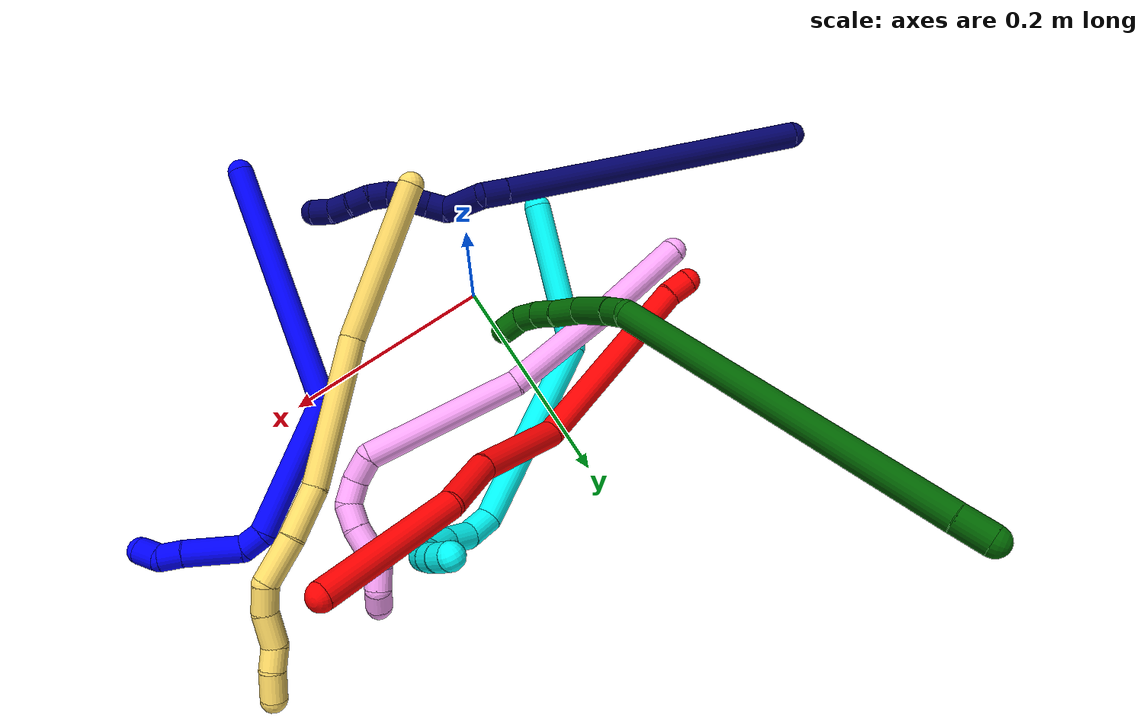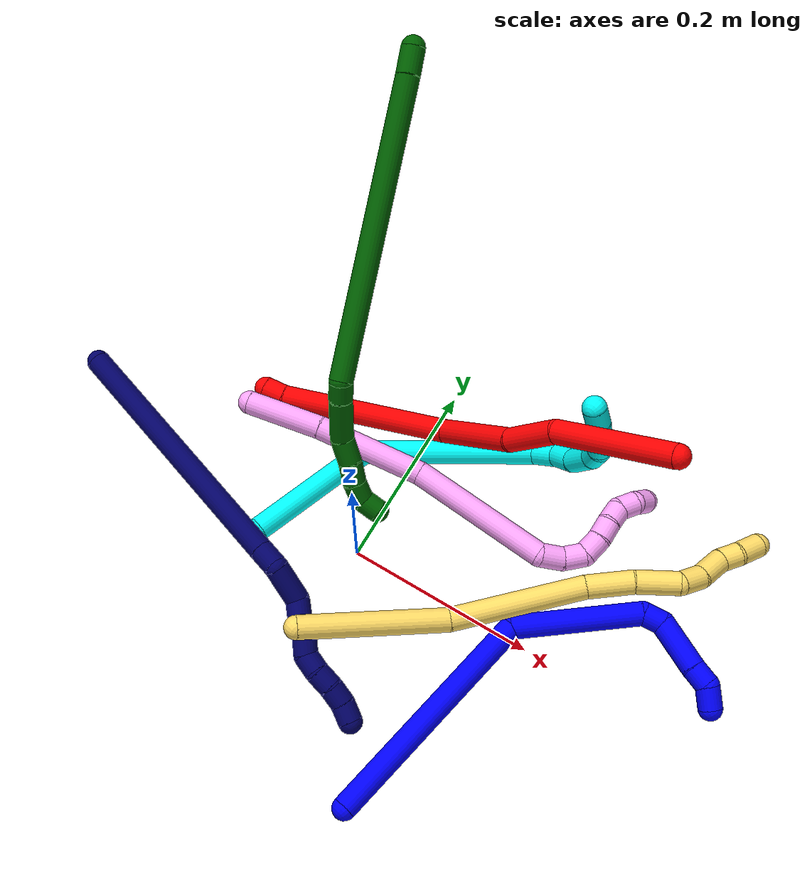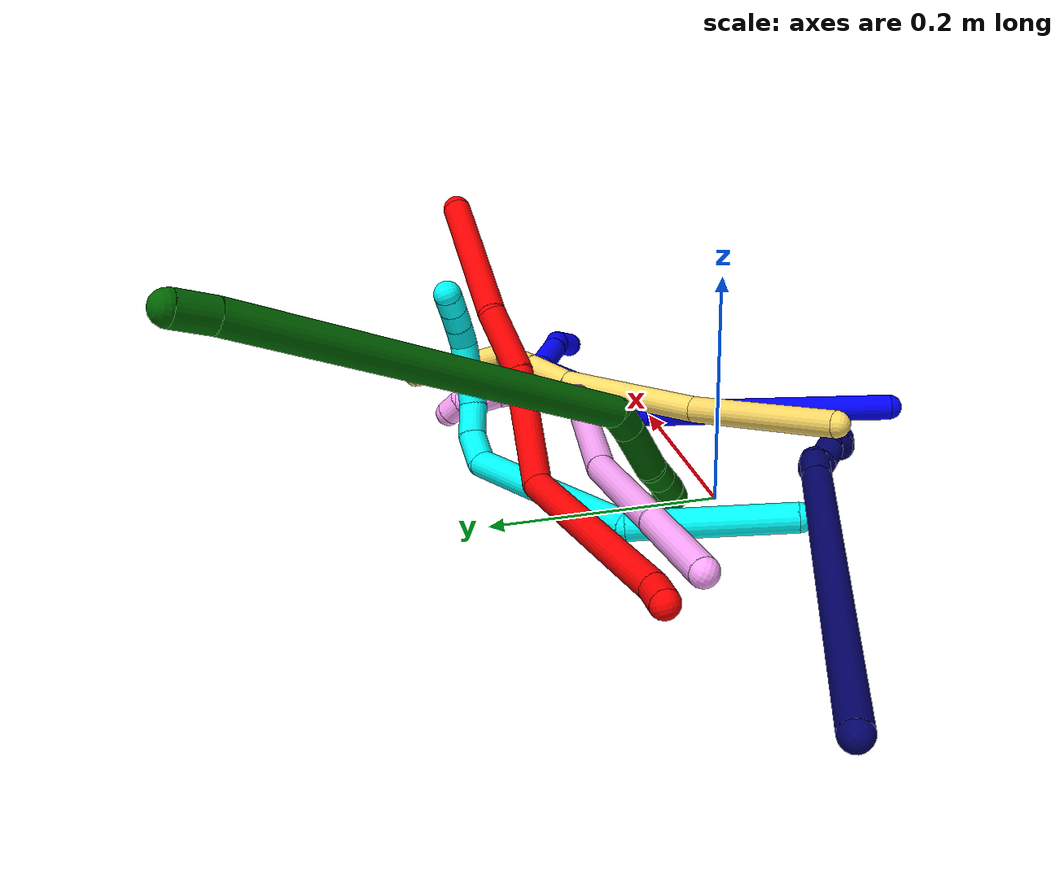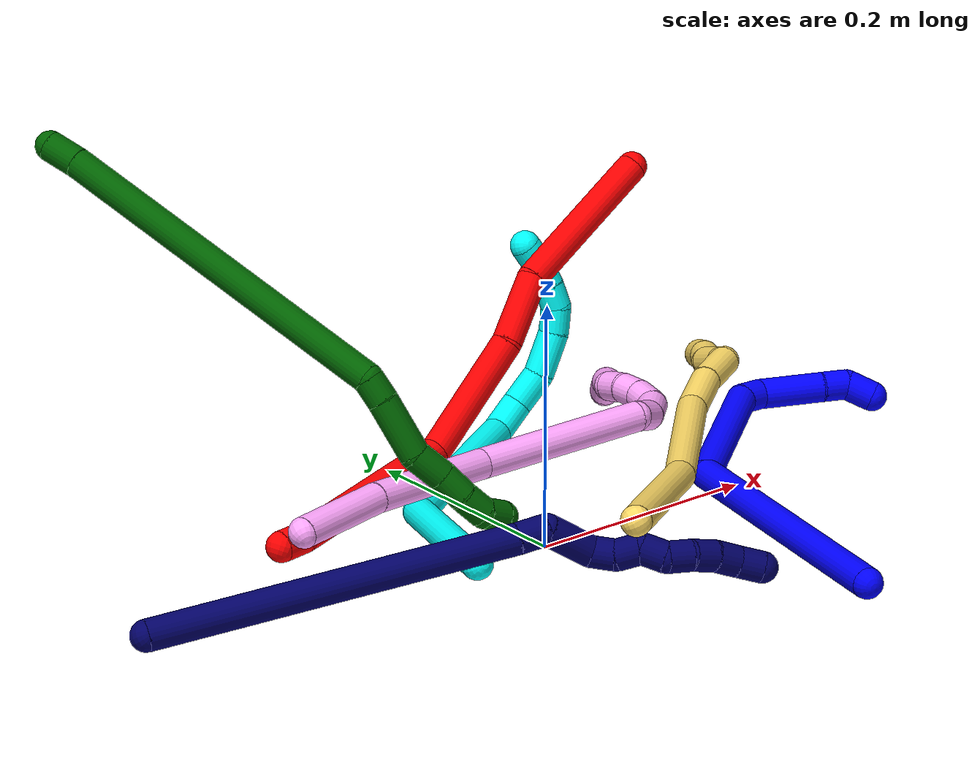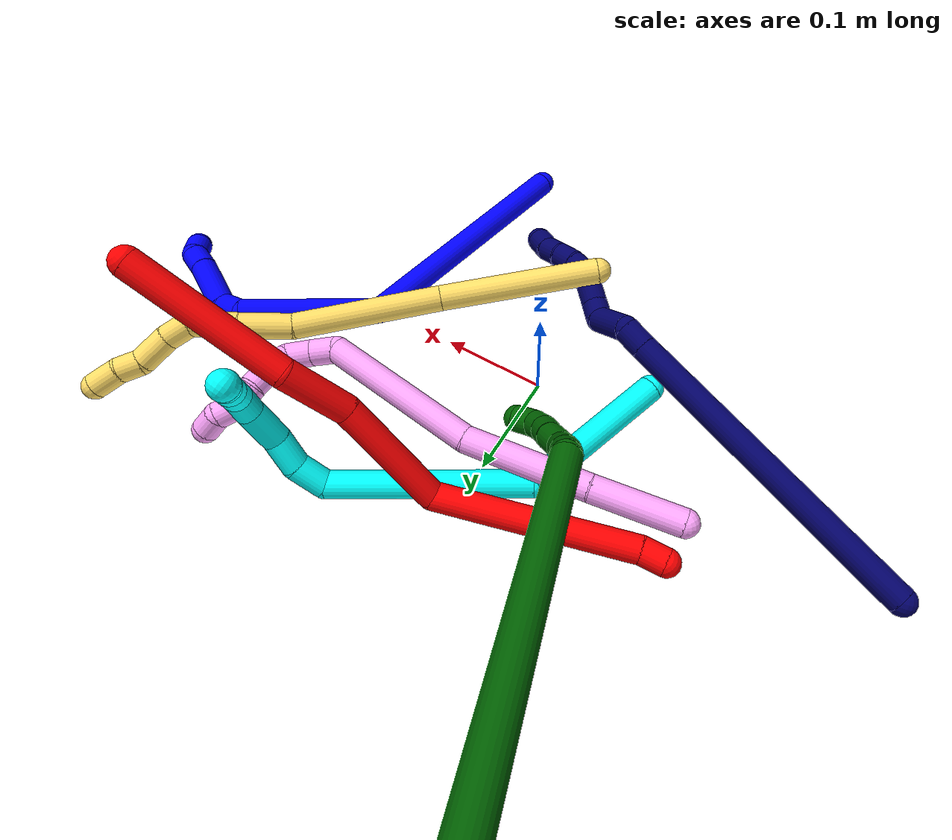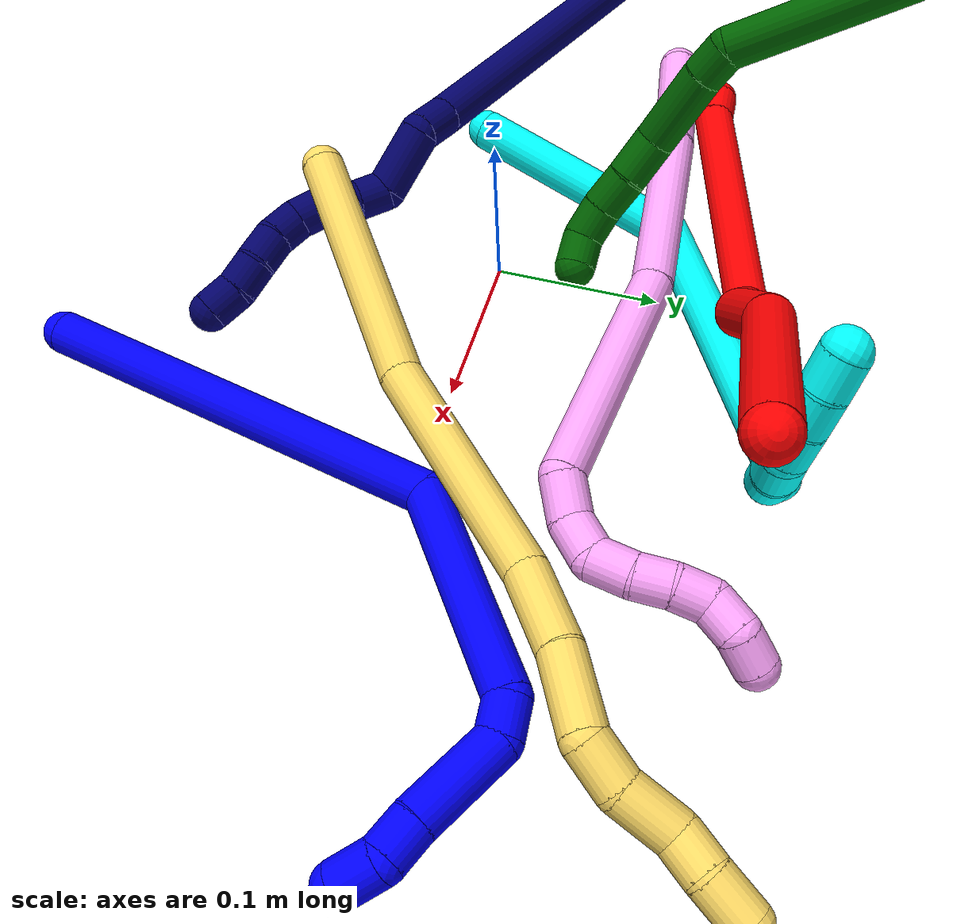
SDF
<sdf version="1.7">
 <world name="default">
  <plugin name="TubeGeneratorPlugin" filename="libtube_generator_plugin.so"/>
  <model name="photoneo_s_sensor">
   <static>1</static>
   <pose>0 0 2 1.57079 1.57079 3.14159</pose>
   <link name="link">
    <inertial><mass>0.1</mass></inertial>
    <sensor name="sensor" type="depth">
     <update_rate>30</update_rate>
     <camera>
      <horizontal_fov>1.22</horizontal_fov>
      <image><width>1920</width><height>1200</height><format>B8G8R8</format></image>
      <clip><near>0.1</near><far>4</far></clip>
      <depth_camera><output>points</output></depth_camera>
     </camera>
     <plugin name="camera_plugin" filename="libgazebo_ros_depth_camera.so">
      <baseline>0.2</baseline>
      <alwaysOn>1</alwaysOn>
      <updateRate>0.0</updateRate>
      <cameraName>camera_ir</cameraName>
      <imageTopicName>/camera/color/image_raw</imageTopicName>
      <cameraInfoTopicName>/camera/color/camera_info</cameraInfoTopicName>
      <depthImageTopicName>/camera/depth/image_raw</depthImageTopicName>
      <depthImageCameraInfoTopicName>/camera/depth/camera_info</depthImageCameraInfoTopicName>
      <pointCloudTopicName>/camera/depth/points</pointCloudTopicName>
      <frameName>fr_optical</frameName>
      <pointCloudCutoff>0.1</pointCloudCutoff>
      <pointCloudCutoffMax>2.0</pointCloudCutoffMax>
      <distortionK1>0</distortionK1>
      <distortionK2>0</distortionK2>
      <distortionK3>0</distortionK3>
      <distortionT1>0</distortionT1>
      <distortionT2>0</distortionT2>
      <CxPrime>0</CxPrime>
      <Cx>0</Cx>
      <Cy>0</Cy>
      <focalLength>0</focalLength>
      <hackBaseline>0</hackBaseline>
     </plugin>
    </sensor>
   </link>
  </model>
  <gravity>0 0 -9.8</gravity>
  <magnetic_field>6e-06 2.3e-05 -4.2e-05</magnetic_field>
  <atmosphere type="adiabatic"/>
  <physics name="default_physics" default="0" type="ode">
   <max_step_size>0.003</max_step_size>
   <real_time_factor>1</real_time_factor>
   <real_time_update_rate>1000</real_time_update_rate>
   <max_contacts>10000</max_contacts>
   <ode>
    <solver>
     <type>quick</type>
     <iters>100</iters>
     <sor>1.3</sor>
     <use_dynamic_moi_rescaling>0</use_dynamic_moi_rescaling>
    </solver>
    <constraints>
     <contact_max_correcting_vel>0</contact_max_correcting_vel>
     <contact_surface_layer>0.001</contact_surface_layer>
     <cfm>0</cfm>
     <erp>0.2</erp>
    </constraints>
   </ode>
  </physics>
  <scene><ambient>0.4 0.4 0.4 1</ambient><background>0.7 0.7 0.7 1</background><shadows>0</shadows></scene>
  <audio><device>default</device></audio>
  <spherical_coordinates>
   <surface_model>EARTH_WGS84</surface_model>
   <latitude_deg>0</latitude_deg>
   <longitude_deg>0</longitude_deg>
   <elevation>0</elevation>
   <heading_deg>0</heading_deg>
  </spherical_coordinates>
  <model name="bin">
   <static>1</static>
   <link name="bottom">
    <collision name="collision-bottom">
     <pose>0 0 -0.01 0 -0 0</pose>
     <geometry><box><size>0.8 0.6 0.02</size></box></geometry>
     <surface>
      <friction><ode><mu>100</mu><mu2>100</mu2></ode></friction>
      <contact><collide_bitmask>65535</collide_bitmask></contact>
     </surface>
    </collision>
   </link>
   <link name="west_wall">
    <collision name="collision-west_wall">
     <pose>-0.41 0 0.1 0 -0 0</pose>
     <geometry><box><size>0.02 0.6 0.2</size></box></geometry>
     <surface>
      <friction><ode><mu>100</mu><mu2>100</mu2></ode></friction>
      <contact><collide_bitmask>65535</collide_bitmask></contact>
     </surface>
    </collision>
   </link>
   <link name="east_wall">
    <collision name="collision-east_wall">
     <pose>0.41 0 0.1 0 -0 0</pose>
     <geometry><box><size>0.02 0.6 0.2</size></box></geometry>
     <surface>
      <friction><ode><mu>100</mu><mu2>100</mu2></ode></friction>
      <contact><collide_bitmask>65535</collide_bitmask></contact>
     </surface>
    </collision>
   </link>
   <link name="south_wall">
    <collision name="collision-south_wall">
     <pose>0 -0.31 0.1 0 -0 0</pose>
     <geometry><box><size>0.8 0.02 0.2</size></box></geometry>
     <surface>
      <friction><ode><mu>100</mu><mu2>100</mu2></ode></friction>
      <contact><collide_bitmask>65535</collide_bitmask></contact>
     </surface>
    </collision>
   </link>
   <link name="north_wall">
    <collision name="collision-north_wall">
     <pose>0 0.31 0.1 0 -0 0</pose>
     <geometry><box><size>0.8 0.02 0.2</size></box></geometry>
     <surface>
      <friction><ode><mu>100</mu><mu2>100</mu2></ode></friction>
      <contact><collide_bitmask>65535</collide_bitmask></contact>
     </surface>
    </collision>
   </link>
  </model>
  <model name="1">
   <static>0</static>
   <link name="1">
    <collision name="collision-cylinder-e_1_1_4">
     <pose>0.000174 -0.000867 0.122832 0.007061 0.00142 5e-06</pose>
     <geometry><cylinder><radius>0.0125</radius><length>0.245671</length></cylinder></geometry>
     <surface>
      <friction><ode><mu>1.16</mu><mu2>1.16</mu2><slip1>0</slip1><slip2>0</slip2></ode></friction>
      <contact><ode><kp>1e+06</kp><kd>1</kd><max_vel>0</max_vel><min_depth>0.001</min_depth></ode></contact>
     </surface>
    </collision>
    <visual name="visual-cylinder-e_1_1_4">
     <pose>0.000174 -0.000867 0.122832 0.007061 0.00142 5e-06</pose>
     <geometry><cylinder><radius>0.0125</radius><length>0.245671</length></cylinder></geometry>
     <material><ambient>0 0 1 1</ambient></material>
    </visual>
    <collision name="collision-cylinder-e_2_4_5">
     <pose>0.040699 0.018698 0.295064 -0.392188 0.646567 -0.132912</pose>
     <geometry><cylinder><radius>0.0125</radius><length>0.133954</length></cylinder></geometry>
     <surface>
      <friction><ode><mu>1.16</mu><mu2>1.16</mu2><slip1>0</slip1><slip2>0</slip2></ode></friction>
      <contact><ode><kp>1e+06</kp><kd>1</kd><max_vel>0</max_vel><min_depth>0.001</min_depth></ode></contact>
     </surface>
    </collision>
    <visual name="visual-cylinder-e_2_4_5">
     <pose>0.040699 0.018698 0.295064 -0.392188 0.646567 -0.132912</pose>
     <geometry><cylinder><radius>0.0125</radius><length>0.133954</length></cylinder></geometry>
     <material><ambient>0 0 1 1</ambient></material>
    </visual>
    <collision name="collision-cylinder-e_3_5_6">
     <pose>0.08894 0.04587 0.347533 -1.14339 0.817058 -0.543235</pose>
     <geometry><cylinder><radius>0.0125</radius><length>0.021644</length></cylinder></geometry>
     <surface>
      <friction><ode><mu>1.16</mu><mu2>1.16</mu2><slip1>0</slip1><slip2>0</slip2></ode></friction>
      <contact><ode><kp>1e+06</kp><kd>1</kd><max_vel>0</max_vel><min_depth>0.001</min_depth></ode></contact>
     </surface>
    </collision>
    <visual name="visual-cylinder-e_3_5_6">
     <pose>0.08894 0.04587 0.347533 -1.14339 0.817058 -0.543235</pose>
     <geometry><cylinder><radius>0.0125</radius><length>0.021644</length></cylinder></geometry>
     <material><ambient>0 0 1 1</ambient></material>
    </visual>
    <collision name="collision-cylinder-e_4_6_7">
     <pose>0.118277 0.066897 0.343125 -2.05298 0.926063 -1.37932</pose>
     <geometry><cylinder><radius>0.0125</radius><length>0.053665</length></cylinder></geometry>
     <surface>
      <friction><ode><mu>1.16</mu><mu2>1.16</mu2><slip1>0</slip1><slip2>0</slip2></ode></friction>
      <contact><ode><kp>1e+06</kp><kd>1</kd><max_vel>0</max_vel><min_depth>0.001</min_depth></ode></contact>
     </surface>
    </collision>
    <visual name="visual-cylinder-e_4_6_7">
     <pose>0.118277 0.066897 0.343125 -2.05298 0.926063 -1.37932</pose>
     <geometry><cylinder><radius>0.0125</radius><length>0.053665</length></cylinder></geometry>
     <material><ambient>0 0 1 1</ambient></material>
    </visual>
    <collision name="collision-cylinder-e_5_7_8">
     <pose>0.14824 0.087439 0.333705 -1.87197 0.915268 -1.17883</pose>
     <geometry><cylinder><radius>0.0125</radius><length>0.021488</length></cylinder></geometry>
     <surface>
      <friction><ode><mu>1.16</mu><mu2>1.16</mu2><slip1>0</slip1><slip2>0</slip2></ode></friction>
      <contact><ode><kp>1e+06</kp><kd>1</kd><max_vel>0</max_vel><min_depth>0.001</min_depth></ode></contact>
     </surface>
    </collision>
    <visual name="visual-cylinder-e_5_7_8">
     <pose>0.14824 0.087439 0.333705 -1.87197 0.915268 -1.17883</pose>
     <geometry><cylinder><radius>0.0125</radius><length>0.021488</length></cylinder></geometry>
     <material><ambient>0 0 1 1</ambient></material>
    </visual>
    <collision name="collision-cylinder-e_6_8_2">
     <pose>0.160942 0.102368 0.324964 -2.2355 0.362919 -0.72086</pose>
     <geometry><cylinder><radius>0.0125</radius><length>0.023579</length></cylinder></geometry>
     <surface>
      <friction><ode><mu>1.16</mu><mu2>1.16</mu2><slip1>0</slip1><slip2>0</slip2></ode></friction>
      <contact><ode><kp>1e+06</kp><kd>1</kd><max_vel>0</max_vel><min_depth>0.001</min_depth></ode></contact>
     </surface>
    </collision>
    <visual name="visual-cylinder-e_6_8_2">
     <pose>0.160942 0.102368 0.324964 -2.2355 0.362919 -0.72086</pose>
     <geometry><cylinder><radius>0.0125</radius><length>0.023579</length></cylinder></geometry>
     <material><ambient>0 0 1 1</ambient></material>
    </visual>
    <collision name="collision-sphere-2">
     <pose>0.165127 0.111043 0.318165 0 -0 0</pose>
     <geometry><sphere><radius>0.0125</radius></sphere></geometry>
     <surface>
      <friction><ode><mu>1.16</mu><mu2>1.16</mu2><slip1>0</slip1><slip2>0</slip2></ode></friction>
      <contact><ode><kp>1e+06</kp><kd>1</kd><max_vel>0</max_vel><min_depth>0.001</min_depth></ode></contact>
     </surface>
    </collision>
    <visual name="visual-sphere-2">
     <pose>0.165127 0.111043 0.318165 0 -0 0</pose>
     <geometry><sphere><radius>0.0125</radius></sphere></geometry>
     <material><ambient>0 0 1 1</ambient></material>
    </visual>
    <collision name="collision-sphere-4">
     <pose>0.000349 -0.001735 0.245665 0 -0 0</pose>
     <geometry><sphere><radius>0.0125</radius></sphere></geometry>
     <surface>
      <friction><ode><mu>1.16</mu><mu2>1.16</mu2><slip1>0</slip1><slip2>0</slip2></ode></friction>
      <contact><ode><kp>1e+06</kp><kd>1</kd><max_vel>0</max_vel><min_depth>0.001</min_depth></ode></contact>
     </surface>
    </collision>
    <visual name="visual-sphere-4">
     <pose>0.000349 -0.001735 0.245665 0 -0 0</pose>
     <geometry><sphere><radius>0.0125</radius></sphere></geometry>
     <material><ambient>0 0 1 1</ambient></material>
    </visual>
    <collision name="collision-sphere-1">
     <geometry><sphere><radius>0.0125</radius></sphere></geometry>
     <surface>
      <friction><ode><mu>1.16</mu><mu2>1.16</mu2><slip1>0</slip1><slip2>0</slip2></ode></friction>
      <contact><ode><kp>1e+06</kp><kd>1</kd><max_vel>0</max_vel><min_depth>0.001</min_depth></ode></contact>
     </surface>
    </collision>
    <visual name="visual-sphere-1">
     <geometry><sphere><radius>0.0125</radius></sphere></geometry>
     <material><ambient>0 0 1 1</ambient></material>
    </visual>
    <collision name="collision-sphere-8">
     <pose>0.156757 0.093693 0.331762 0 -0 0</pose>
     <geometry><sphere><radius>0.0125</radius></sphere></geometry>
     <surface>
      <friction><ode><mu>1.16</mu><mu2>1.16</mu2><slip1>0</slip1><slip2>0</slip2></ode></friction>
      <contact><ode><kp>1e+06</kp><kd>1</kd><max_vel>0</max_vel><min_depth>0.001</min_depth></ode></contact>
     </surface>
    </collision>
    <visual name="visual-sphere-8">
     <pose>0.156757 0.093693 0.331762 0 -0 0</pose>
     <geometry><sphere><radius>0.0125</radius></sphere></geometry>
     <material><ambient>0 0 1 1</ambient></material>
    </visual>
    <collision name="collision-sphere-5">
     <pose>0.08105 0.03913 0.344463 0 -0 0</pose>
     <geometry><sphere><radius>0.0125</radius></sphere></geometry>
     <surface>
      <friction><ode><mu>1.16</mu><mu2>1.16</mu2><slip1>0</slip1><slip2>0</slip2></ode></friction>
      <contact><ode><kp>1e+06</kp><kd>1</kd><max_vel>0</max_vel><min_depth>0.001</min_depth></ode></contact>
     </surface>
    </collision>
    <visual name="visual-sphere-5">
     <pose>0.08105 0.03913 0.344463 0 -0 0</pose>
     <geometry><sphere><radius>0.0125</radius></sphere></geometry>
     <material><ambient>0 0 1 1</ambient></material>
    </visual>
    <collision name="collision-sphere-6">
     <pose>0.096831 0.05261 0.350603 0 -0 0</pose>
     <geometry><sphere><radius>0.0125</radius></sphere></geometry>
     <surface>
      <friction><ode><mu>1.16</mu><mu2>1.16</mu2><slip1>0</slip1><slip2>0</slip2></ode></friction>
      <contact><ode><kp>1e+06</kp><kd>1</kd><max_vel>0</max_vel><min_depth>0.001</min_depth></ode></contact>
     </surface>
    </collision>
    <visual name="visual-sphere-6">
     <pose>0.096831 0.05261 0.350603 0 -0 0</pose>
     <geometry><sphere><radius>0.0125</radius></sphere></geometry>
     <material><ambient>0 0 1 1</ambient></material>
    </visual>
    <collision name="collision-sphere-7">
     <pose>0.139723 0.081184 0.335648 0 -0 0</pose>
     <geometry><sphere><radius>0.0125</radius></sphere></geometry>
     <surface>
      <friction><ode><mu>1.16</mu><mu2>1.16</mu2><slip1>0</slip1><slip2>0</slip2></ode></friction>
      <contact><ode><kp>1e+06</kp><kd>1</kd><max_vel>0</max_vel><min_depth>0.001</min_depth></ode></contact>
     </surface>
    </collision>
    <visual name="visual-sphere-7">
     <pose>0.139723 0.081184 0.335648 0 -0 0</pose>
     <geometry><sphere><radius>0.0125</radius></sphere></geometry>
     <material><ambient>0 0 1 1</ambient></material>
    </visual>
    <inertial>
     <pose>0.041494 0.022334 0.22094 0 -0 0</pose>
     <mass>0.5</mass>
     <inertia>
      <ixx>0.001392</ixx>
      <ixy>0</ixy>
      <ixz>0</ixz>
      <iyy>0.001426</iyy>
      <iyz>0</iyz>
      <izz>-0.000181</izz>
     </inertia>
    </inertial>
   </link>
   <pose>0.125865 -0.229418 0.013203 -1.58327 -0.634676 -0.20636</pose>
  </model>
  <model name="2">
   <static>0</static>
   <link name="2">
    <collision name="collision-cylinder-e_1_1_4">
     <pose>0.009162 0.001611 0.006476 -0.243884 0.94127 -0.124537</pose>
     <geometry><cylinder><radius>0.0125</radius><length>0.02267</length></cylinder></geometry>
     <surface>
      <friction><ode><mu>1.16</mu><mu2>1.16</mu2><slip1>0</slip1><slip2>0</slip2></ode></friction>
      <contact><ode><kp>1e+06</kp><kd>1</kd><max_vel>0</max_vel><min_depth>0.001</min_depth></ode></contact>
     </surface>
    </collision>
    <visual name="visual-cylinder-e_1_1_4">
     <pose>0.009162 0.001611 0.006476 -0.243884 0.94127 -0.124537</pose>
     <geometry><cylinder><radius>0.0125</radius><length>0.02267</length></cylinder></geometry>
     <material><ambient>1 0 0 1</ambient></material>
    </visual>
    <collision name="collision-cylinder-e_2_4_5">
     <pose>0.083038 0.034474 0.065714 -0.534744 0.812299 -0.234533</pose>
     <geometry><cylinder><radius>0.0125</radius><length>0.178306</length></cylinder></geometry>
     <surface>
      <friction><ode><mu>1.16</mu><mu2>1.16</mu2><slip1>0</slip1><slip2>0</slip2></ode></friction>
      <contact><ode><kp>1e+06</kp><kd>1</kd><max_vel>0</max_vel><min_depth>0.001</min_depth></ode></contact>
     </surface>
    </collision>
    <visual name="visual-cylinder-e_2_4_5">
     <pose>0.083038 0.034474 0.065714 -0.534744 0.812299 -0.234533</pose>
     <geometry><cylinder><radius>0.0125</radius><length>0.178306</length></cylinder></geometry>
     <material><ambient>1 0 0 1</ambient></material>
    </visual>
    <collision name="collision-cylinder-e_3_5_6">
     <pose>0.160251 0.060441 0.169594 0.102998 0.238597 0.012357</pose>
     <geometry><cylinder><radius>0.0125</radius><length>0.105779</length></cylinder></geometry>
     <surface>
      <friction><ode><mu>1.16</mu><mu2>1.16</mu2><slip1>0</slip1><slip2>0</slip2></ode></friction>
      <contact><ode><kp>1e+06</kp><kd>1</kd><max_vel>0</max_vel><min_depth>0.001</min_depth></ode></contact>
     </surface>
    </collision>
    <visual name="visual-cylinder-e_3_5_6">
     <pose>0.160251 0.060441 0.169594 0.102998 0.238597 0.012357</pose>
     <geometry><cylinder><radius>0.0125</radius><length>0.105779</length></cylinder></geometry>
     <material><ambient>1 0 0 1</ambient></material>
    </visual>
    <collision name="collision-cylinder-e_4_6_7">
     <pose>0.177451 0.059719 0.249682 -0.156159 0.158908 -0.012459</pose>
     <geometry><cylinder><radius>0.0125</radius><length>0.059401</length></cylinder></geometry>
     <surface>
      <friction><ode><mu>1.16</mu><mu2>1.16</mu2><slip1>0</slip1><slip2>0</slip2></ode></friction>
      <contact><ode><kp>1e+06</kp><kd>1</kd><max_vel>0</max_vel><min_depth>0.001</min_depth></ode></contact>
     </surface>
    </collision>
    <visual name="visual-cylinder-e_4_6_7">
     <pose>0.177451 0.059719 0.249682 -0.156159 0.158908 -0.012459</pose>
     <geometry><cylinder><radius>0.0125</radius><length>0.059401</length></cylinder></geometry>
     <material><ambient>1 0 0 1</ambient></material>
    </visual>
    <collision name="collision-cylinder-e_5_7_2">
     <pose>0.213005 0.067095 0.33797 -0.047422 0.479172 -0.011586</pose>
     <geometry><cylinder><radius>0.0125</radius><length>0.133844</length></cylinder></geometry>
     <surface>
      <friction><ode><mu>1.16</mu><mu2>1.16</mu2><slip1>0</slip1><slip2>0</slip2></ode></friction>
      <contact><ode><kp>1e+06</kp><kd>1</kd><max_vel>0</max_vel><min_depth>0.001</min_depth></ode></contact>
     </surface>
    </collision>
    <visual name="visual-cylinder-e_5_7_2">
     <pose>0.213005 0.067095 0.33797 -0.047422 0.479172 -0.011586</pose>
     <geometry><cylinder><radius>0.0125</radius><length>0.133844</length></cylinder></geometry>
     <material><ambient>1 0 0 1</ambient></material>
    </visual>
    <collision name="collision-sphere-2">
     <pose>0.243859 0.06991 0.397289 0 -0 0</pose>
     <geometry><sphere><radius>0.0125</radius></sphere></geometry>
     <surface>
      <friction><ode><mu>1.16</mu><mu2>1.16</mu2><slip1>0</slip1><slip2>0</slip2></ode></friction>
      <contact><ode><kp>1e+06</kp><kd>1</kd><max_vel>0</max_vel><min_depth>0.001</min_depth></ode></contact>
     </surface>
    </collision>
    <visual name="visual-sphere-2">
     <pose>0.243859 0.06991 0.397289 0 -0 0</pose>
     <geometry><sphere><radius>0.0125</radius></sphere></geometry>
     <material><ambient>1 0 0 1</ambient></material>
    </visual>
    <collision name="collision-sphere-7">
     <pose>0.182151 0.06428 0.278652 0 -0 0</pose>
     <geometry><sphere><radius>0.0125</radius></sphere></geometry>
     <surface>
      <friction><ode><mu>1.16</mu><mu2>1.16</mu2><slip1>0</slip1><slip2>0</slip2></ode></friction>
      <contact><ode><kp>1e+06</kp><kd>1</kd><max_vel>0</max_vel><min_depth>0.001</min_depth></ode></contact>
     </surface>
    </collision>
    <visual name="visual-sphere-7">
     <pose>0.182151 0.06428 0.278652 0 -0 0</pose>
     <geometry><sphere><radius>0.0125</radius></sphere></geometry>
     <material><ambient>1 0 0 1</ambient></material>
    </visual>
    <collision name="collision-sphere-6">
     <pose>0.172751 0.055158 0.220713 0 -0 0</pose>
     <geometry><sphere><radius>0.0125</radius></sphere></geometry>
     <surface>
      <friction><ode><mu>1.16</mu><mu2>1.16</mu2><slip1>0</slip1><slip2>0</slip2></ode></friction>
      <contact><ode><kp>1e+06</kp><kd>1</kd><max_vel>0</max_vel><min_depth>0.001</min_depth></ode></contact>
     </surface>
    </collision>
    <visual name="visual-sphere-6">
     <pose>0.172751 0.055158 0.220713 0 -0 0</pose>
     <geometry><sphere><radius>0.0125</radius></sphere></geometry>
     <material><ambient>1 0 0 1</ambient></material>
    </visual>
    <collision name="collision-sphere-5">
     <pose>0.147751 0.065725 0.118476 0 -0 0</pose>
     <geometry><sphere><radius>0.0125</radius></sphere></geometry>
     <surface>
      <friction><ode><mu>1.16</mu><mu2>1.16</mu2><slip1>0</slip1><slip2>0</slip2></ode></friction>
      <contact><ode><kp>1e+06</kp><kd>1</kd><max_vel>0</max_vel><min_depth>0.001</min_depth></ode></contact>
     </surface>
    </collision>
    <visual name="visual-sphere-5">
     <pose>0.147751 0.065725 0.118476 0 -0 0</pose>
     <geometry><sphere><radius>0.0125</radius></sphere></geometry>
     <material><ambient>1 0 0 1</ambient></material>
    </visual>
    <collision name="collision-sphere-1">
     <geometry><sphere><radius>0.0125</radius></sphere></geometry>
     <surface>
      <friction><ode><mu>1.16</mu><mu2>1.16</mu2><slip1>0</slip1><slip2>0</slip2></ode></friction>
      <contact><ode><kp>1e+06</kp><kd>1</kd><max_vel>0</max_vel><min_depth>0.001</min_depth></ode></contact>
     </surface>
    </collision>
    <visual name="visual-sphere-1">
     <geometry><sphere><radius>0.0125</radius></sphere></geometry>
     <material><ambient>1 0 0 1</ambient></material>
    </visual>
    <collision name="collision-sphere-4">
     <pose>0.018324 0.003223 0.012952 0 -0 0</pose>
     <geometry><sphere><radius>0.0125</radius></sphere></geometry>
     <surface>
      <friction><ode><mu>1.16</mu><mu2>1.16</mu2><slip1>0</slip1><slip2>0</slip2></ode></friction>
      <contact><ode><kp>1e+06</kp><kd>1</kd><max_vel>0</max_vel><min_depth>0.001</min_depth></ode></contact>
     </surface>
    </collision>
    <visual name="visual-sphere-4">
     <pose>0.018324 0.003223 0.012952 0 -0 0</pose>
     <geometry><sphere><radius>0.0125</radius></sphere></geometry>
     <material><ambient>1 0 0 1</ambient></material>
    </visual>
    <inertial>
     <pose>0.14203 0.050209 0.17974 0 -0 0</pose>
     <mass>0.5</mass>
     <inertia>
      <ixx>0.000564</ixx>
      <ixy>0</ixy>
      <ixz>0</ixz>
      <iyy>0.000698</iyy>
      <iyz>0</iyz>
      <izz>-0.00061</izz>
     </inertia>
    </inertial>
   </link>
   <pose>-0.178806 0.103043 0.013856 -0.250214 0.51243 -0.218898</pose>
  </model>
  <model name="3">
   <static>0</static>
   <link name="3">
    <collision name="collision-cylinder-e_1_1_4">
     <pose>0.017217 0.015196 0.066471 -0.224749 0.24733 -0.028053</pose>
     <geometry><cylinder><radius>0.0125</radius><length>0.140652</length></cylinder></geometry>
     <surface>
      <friction><ode><mu>1.16</mu><mu2>1.16</mu2><slip1>0</slip1><slip2>0</slip2></ode></friction>
      <contact><ode><kp>1e+06</kp><kd>1</kd><max_vel>0</max_vel><min_depth>0.001</min_depth></ode></contact>
     </surface>
    </collision>
    <visual name="visual-cylinder-e_1_1_4">
     <pose>0.017217 0.015196 0.066471 -0.224749 0.24733 -0.028053</pose>
     <geometry><cylinder><radius>0.0125</radius><length>0.140652</length></cylinder></geometry>
     <material><ambient>0.003922 1 0.996078 1</ambient></material>
    </visual>
    <collision name="collision-cylinder-e_2_4_5">
     <pose>0.051791 0.10181 0.185427 -0.937025 0.193386 -0.098099</pose>
     <geometry><cylinder><radius>0.0125</radius><length>0.180627</length></cylinder></geometry>
     <surface>
      <friction><ode><mu>1.16</mu><mu2>1.16</mu2><slip1>0</slip1><slip2>0</slip2></ode></friction>
      <contact><ode><kp>1e+06</kp><kd>1</kd><max_vel>0</max_vel><min_depth>0.001</min_depth></ode></contact>
     </surface>
    </collision>
    <visual name="visual-cylinder-e_2_4_5">
     <pose>0.051791 0.10181 0.185427 -0.937025 0.193386 -0.098099</pose>
     <geometry><cylinder><radius>0.0125</radius><length>0.180627</length></cylinder></geometry>
     <material><ambient>0.003922 1 0.996078 1</ambient></material>
    </visual>
    <collision name="collision-cylinder-e_3_5_6">
     <pose>0.078241 0.185307 0.238109 -1.55457 0.645284 -0.635588</pose>
     <geometry><cylinder><radius>0.0125</radius><length>0.030241</length></cylinder></geometry>
     <surface>
      <friction><ode><mu>1.16</mu><mu2>1.16</mu2><slip1>0</slip1><slip2>0</slip2></ode></friction>
      <contact><ode><kp>1e+06</kp><kd>1</kd><max_vel>0</max_vel><min_depth>0.001</min_depth></ode></contact>
     </surface>
    </collision>
    <visual name="visual-cylinder-e_3_5_6">
     <pose>0.078241 0.185307 0.238109 -1.55457 0.645284 -0.635588</pose>
     <geometry><cylinder><radius>0.0125</radius><length>0.030241</length></cylinder></geometry>
     <material><ambient>0.003922 1 0.996078 1</ambient></material>
    </visual>
    <collision name="collision-cylinder-e_4_6_7">
     <pose>0.097221 0.207239 0.233168 -2.05133 0.727054 -1.12055</pose>
     <geometry><cylinder><radius>0.0125</radius><length>0.029746</length></cylinder></geometry>
     <surface>
      <friction><ode><mu>1.16</mu><mu2>1.16</mu2><slip1>0</slip1><slip2>0</slip2></ode></friction>
      <contact><ode><kp>1e+06</kp><kd>1</kd><max_vel>0</max_vel><min_depth>0.001</min_depth></ode></contact>
     </surface>
    </collision>
    <visual name="visual-cylinder-e_4_6_7">
     <pose>0.097221 0.207239 0.233168 -2.05133 0.727054 -1.12055</pose>
     <geometry><cylinder><radius>0.0125</radius><length>0.029746</length></cylinder></geometry>
     <material><ambient>0.003922 1 0.996078 1</ambient></material>
    </visual>
    <collision name="collision-cylinder-e_5_7_8">
     <pose>0.122799 0.225855 0.224169 -1.98602 1.02289 -1.42148</pose>
     <geometry><cylinder><radius>0.0125</radius><length>0.036767</length></cylinder></geometry>
     <surface>
      <friction><ode><mu>1.16</mu><mu2>1.16</mu2><slip1>0</slip1><slip2>0</slip2></ode></friction>
      <contact><ode><kp>1e+06</kp><kd>1</kd><max_vel>0</max_vel><min_depth>0.001</min_depth></ode></contact>
     </surface>
    </collision>
    <visual name="visual-cylinder-e_5_7_8">
     <pose>0.122799 0.225855 0.224169 -1.98602 1.02289 -1.42148</pose>
     <geometry><cylinder><radius>0.0125</radius><length>0.036767</length></cylinder></geometry>
     <material><ambient>0.003922 1 0.996078 1</ambient></material>
    </visual>
    <collision name="collision-cylinder-e_6_8_9">
     <pose>0.148856 0.236702 0.217647 -2.47685 1.25569 -2.25377</pose>
     <geometry><cylinder><radius>0.0125</radius><length>0.021803</length></cylinder></geometry>
     <surface>
      <friction><ode><mu>1.16</mu><mu2>1.16</mu2><slip1>0</slip1><slip2>0</slip2></ode></friction>
      <contact><ode><kp>1e+06</kp><kd>1</kd><max_vel>0</max_vel><min_depth>0.001</min_depth></ode></contact>
     </surface>
    </collision>
    <visual name="visual-cylinder-e_6_8_9">
     <pose>0.148856 0.236702 0.217647 -2.47685 1.25569 -2.25377</pose>
     <geometry><cylinder><radius>0.0125</radius><length>0.021803</length></cylinder></geometry>
     <material><ambient>0.003922 1 0.996078 1</ambient></material>
    </visual>
    <collision name="collision-cylinder-e_7_9_10">
     <pose>0.168923 0.236466 0.213656 2.09194 1.3018 1.8416</pose>
     <geometry><cylinder><radius>0.0125</radius><length>0.020127</length></cylinder></geometry>
     <surface>
      <friction><ode><mu>1.16</mu><mu2>1.16</mu2><slip1>0</slip1><slip2>0</slip2></ode></friction>
      <contact><ode><kp>1e+06</kp><kd>1</kd><max_vel>0</max_vel><min_depth>0.001</min_depth></ode></contact>
     </surface>
    </collision>
    <visual name="visual-cylinder-e_7_9_10">
     <pose>0.168923 0.236466 0.213656 2.09194 1.3018 1.8416</pose>
     <geometry><cylinder><radius>0.0125</radius><length>0.020127</length></cylinder></geometry>
     <material><ambient>0.003922 1 0.996078 1</ambient></material>
    </visual>
    <collision name="collision-cylinder-e_8_10_11">
     <pose>0.187922 0.230631 0.211126 1.89951 1.19074 1.51607</pose>
     <geometry><cylinder><radius>0.0125</radius><length>0.020024</length></cylinder></geometry>
     <surface>
      <friction><ode><mu>1.16</mu><mu2>1.16</mu2><slip1>0</slip1><slip2>0</slip2></ode></friction>
      <contact><ode><kp>1e+06</kp><kd>1</kd><max_vel>0</max_vel><min_depth>0.001</min_depth></ode></contact>
     </surface>
    </collision>
    <visual name="visual-cylinder-e_8_10_11">
     <pose>0.187922 0.230631 0.211126 1.89951 1.19074 1.51607</pose>
     <geometry><cylinder><radius>0.0125</radius><length>0.020024</length></cylinder></geometry>
     <material><ambient>0.003922 1 0.996078 1</ambient></material>
    </visual>
    <collision name="collision-cylinder-e_9_11_2">
     <pose>0.205915 0.222276 0.208886 1.78254 1.05319 1.24752</pose>
     <geometry><cylinder><radius>0.0125</radius><length>0.020012</length></cylinder></geometry>
     <surface>
      <friction><ode><mu>1.16</mu><mu2>1.16</mu2><slip1>0</slip1><slip2>0</slip2></ode></friction>
      <contact><ode><kp>1e+06</kp><kd>1</kd><max_vel>0</max_vel><min_depth>0.001</min_depth></ode></contact>
     </surface>
    </collision>
    <visual name="visual-cylinder-e_9_11_2">
     <pose>0.205915 0.222276 0.208886 1.78254 1.05319 1.24752</pose>
     <geometry><cylinder><radius>0.0125</radius><length>0.020012</length></cylinder></geometry>
     <material><ambient>0.003922 1 0.996078 1</ambient></material>
    </visual>
    <collision name="collision-sphere-2">
     <pose>0.214611 0.217435 0.207845 0 -0 0</pose>
     <geometry><sphere><radius>0.0125</radius></sphere></geometry>
     <surface>
      <friction><ode><mu>1.16</mu><mu2>1.16</mu2><slip1>0</slip1><slip2>0</slip2></ode></friction>
      <contact><ode><kp>1e+06</kp><kd>1</kd><max_vel>0</max_vel><min_depth>0.001</min_depth></ode></contact>
     </surface>
    </collision>
    <visual name="visual-sphere-2">
     <pose>0.214611 0.217435 0.207845 0 -0 0</pose>
     <geometry><sphere><radius>0.0125</radius></sphere></geometry>
     <material><ambient>0.003922 1 0.996078 1</ambient></material>
    </visual>
    <collision name="collision-sphere-11">
     <pose>0.19722 0.227116 0.209926 0 -0 0</pose>
     <geometry><sphere><radius>0.0125</radius></sphere></geometry>
     <surface>
      <friction><ode><mu>1.16</mu><mu2>1.16</mu2><slip1>0</slip1><slip2>0</slip2></ode></friction>
      <contact><ode><kp>1e+06</kp><kd>1</kd><max_vel>0</max_vel><min_depth>0.001</min_depth></ode></contact>
     </surface>
    </collision>
    <visual name="visual-sphere-11">
     <pose>0.19722 0.227116 0.209926 0 -0 0</pose>
     <geometry><sphere><radius>0.0125</radius></sphere></geometry>
     <material><ambient>0.003922 1 0.996078 1</ambient></material>
    </visual>
    <collision name="collision-sphere-10">
     <pose>0.178625 0.234147 0.212325 0 -0 0</pose>
     <geometry><sphere><radius>0.0125</radius></sphere></geometry>
     <surface>
      <friction><ode><mu>1.16</mu><mu2>1.16</mu2><slip1>0</slip1><slip2>0</slip2></ode></friction>
      <contact><ode><kp>1e+06</kp><kd>1</kd><max_vel>0</max_vel><min_depth>0.001</min_depth></ode></contact>
     </surface>
    </collision>
    <visual name="visual-sphere-10">
     <pose>0.178625 0.234147 0.212325 0 -0 0</pose>
     <geometry><sphere><radius>0.0125</radius></sphere></geometry>
     <material><ambient>0.003922 1 0.996078 1</ambient></material>
    </visual>
    <collision name="collision-sphere-9">
     <pose>0.159221 0.238786 0.214988 0 -0 0</pose>
     <geometry><sphere><radius>0.0125</radius></sphere></geometry>
     <surface>
      <friction><ode><mu>1.16</mu><mu2>1.16</mu2><slip1>0</slip1><slip2>0</slip2></ode></friction>
      <contact><ode><kp>1e+06</kp><kd>1</kd><max_vel>0</max_vel><min_depth>0.001</min_depth></ode></contact>
     </surface>
    </collision>
    <visual name="visual-sphere-9">
     <pose>0.159221 0.238786 0.214988 0 -0 0</pose>
     <geometry><sphere><radius>0.0125</radius></sphere></geometry>
     <material><ambient>0.003922 1 0.996078 1</ambient></material>
    </visual>
    <collision name="collision-sphere-4">
     <pose>0.034434 0.030392 0.132942 0 -0 0</pose>
     <geometry><sphere><radius>0.0125</radius></sphere></geometry>
     <surface>
      <friction><ode><mu>1.16</mu><mu2>1.16</mu2><slip1>0</slip1><slip2>0</slip2></ode></friction>
      <contact><ode><kp>1e+06</kp><kd>1</kd><max_vel>0</max_vel><min_depth>0.001</min_depth></ode></contact>
     </surface>
    </collision>
    <visual name="visual-sphere-4">
     <pose>0.034434 0.030392 0.132942 0 -0 0</pose>
     <geometry><sphere><radius>0.0125</radius></sphere></geometry>
     <material><ambient>0.003922 1 0.996078 1</ambient></material>
    </visual>
    <collision name="collision-sphere-1">
     <geometry><sphere><radius>0.0125</radius></sphere></geometry>
     <surface>
      <friction><ode><mu>1.16</mu><mu2>1.16</mu2><slip1>0</slip1><slip2>0</slip2></ode></friction>
      <contact><ode><kp>1e+06</kp><kd>1</kd><max_vel>0</max_vel><min_depth>0.001</min_depth></ode></contact>
     </surface>
    </collision>
    <visual name="visual-sphere-1">
     <geometry><sphere><radius>0.0125</radius></sphere></geometry>
     <material><ambient>0.003922 1 0.996078 1</ambient></material>
    </visual>
    <collision name="collision-sphere-8">
     <pose>0.138492 0.234618 0.220306 0 -0 0</pose>
     <geometry><sphere><radius>0.0125</radius></sphere></geometry>
     <surface>
      <friction><ode><mu>1.16</mu><mu2>1.16</mu2><slip1>0</slip1><slip2>0</slip2></ode></friction>
      <contact><ode><kp>1e+06</kp><kd>1</kd><max_vel>0</max_vel><min_depth>0.001</min_depth></ode></contact>
     </surface>
    </collision>
    <visual name="visual-sphere-8">
     <pose>0.138492 0.234618 0.220306 0 -0 0</pose>
     <geometry><sphere><radius>0.0125</radius></sphere></geometry>
     <material><ambient>0.003922 1 0.996078 1</ambient></material>
    </visual>
    <collision name="collision-sphere-5">
     <pose>0.069147 0.173228 0.237913 0 -0 0</pose>
     <geometry><sphere><radius>0.0125</radius></sphere></geometry>
     <surface>
      <friction><ode><mu>1.16</mu><mu2>1.16</mu2><slip1>0</slip1><slip2>0</slip2></ode></friction>
      <contact><ode><kp>1e+06</kp><kd>1</kd><max_vel>0</max_vel><min_depth>0.001</min_depth></ode></contact>
     </surface>
    </collision>
    <visual name="visual-sphere-5">
     <pose>0.069147 0.173228 0.237913 0 -0 0</pose>
     <geometry><sphere><radius>0.0125</radius></sphere></geometry>
     <material><ambient>0.003922 1 0.996078 1</ambient></material>
    </visual>
    <collision name="collision-sphere-6">
     <pose>0.087335 0.197386 0.238305 0 -0 0</pose>
     <geometry><sphere><radius>0.0125</radius></sphere></geometry>
     <surface>
      <friction><ode><mu>1.16</mu><mu2>1.16</mu2><slip1>0</slip1><slip2>0</slip2></ode></friction>
      <contact><ode><kp>1e+06</kp><kd>1</kd><max_vel>0</max_vel><min_depth>0.001</min_depth></ode></contact>
     </surface>
    </collision>
    <visual name="visual-sphere-6">
     <pose>0.087335 0.197386 0.238305 0 -0 0</pose>
     <geometry><sphere><radius>0.0125</radius></sphere></geometry>
     <material><ambient>0.003922 1 0.996078 1</ambient></material>
    </visual>
    <collision name="collision-sphere-7">
     <pose>0.107107 0.217093 0.228032 0 -0 0</pose>
     <geometry><sphere><radius>0.0125</radius></sphere></geometry>
     <surface>
      <friction><ode><mu>1.16</mu><mu2>1.16</mu2><slip1>0</slip1><slip2>0</slip2></ode></friction>
      <contact><ode><kp>1e+06</kp><kd>1</kd><max_vel>0</max_vel><min_depth>0.001</min_depth></ode></contact>
     </surface>
    </collision>
    <visual name="visual-sphere-7">
     <pose>0.107107 0.217093 0.228032 0 -0 0</pose>
     <geometry><sphere><radius>0.0125</radius></sphere></geometry>
     <material><ambient>0.003922 1 0.996078 1</ambient></material>
    </visual>
    <inertial>
     <pose>0.072157 0.119172 0.165349 0 -0 0</pose>
     <mass>0.5</mass>
     <inertia>
      <ixx>0.000677</ixx>
      <ixy>0</ixy>
      <ixz>0</ixz>
      <iyy>0.000502</iyy>
      <iyz>0</iyz>
      <izz>-0.000604</izz>
     </inertia>
    </inertial>
   </link>
   <pose>-0.097089 -0.036046 0.024113 3.07059 -1.21906 1.51653</pose>
  </model>
  <model name="4">
   <static>0</static>
   <link name="4">
    <collision name="collision-cylinder-e_1_1_4">
     <pose>0.028147 -0.025034 -0.015062 2.11244 0.766763 1.23931</pose>
     <geometry><cylinder><radius>0.0125</radius><length>0.081136</length></cylinder></geometry>
     <surface>
      <friction><ode><mu>1.16</mu><mu2>1.16</mu2><slip1>0</slip1><slip2>0</slip2></ode></friction>
      <contact><ode><kp>1e+06</kp><kd>1</kd><max_vel>0</max_vel><min_depth>0.001</min_depth></ode></contact>
     </surface>
    </collision>
    <visual name="visual-cylinder-e_1_1_4">
     <pose>0.028147 -0.025034 -0.015062 2.11244 0.766763 1.23931</pose>
     <geometry><cylinder><radius>0.0125</radius><length>0.081136</length></cylinder></geometry>
     <material><ambient>1 0.65098 0.996078 1</ambient></material>
    </visual>
    <collision name="collision-cylinder-e_2_4_5">
     <pose>0.096207 -0.08878 -0.046435 1.96958 0.759833 1.08314</pose>
     <geometry><cylinder><radius>0.0125</radius><length>0.115894</length></cylinder></geometry>
     <surface>
      <friction><ode><mu>1.16</mu><mu2>1.16</mu2><slip1>0</slip1><slip2>0</slip2></ode></friction>
      <contact><ode><kp>1e+06</kp><kd>1</kd><max_vel>0</max_vel><min_depth>0.001</min_depth></ode></contact>
     </surface>
    </collision>
    <visual name="visual-cylinder-e_2_4_5">
     <pose>0.096207 -0.08878 -0.046435 1.96958 0.759833 1.08314</pose>
     <geometry><cylinder><radius>0.0125</radius><length>0.115894</length></cylinder></geometry>
     <material><ambient>1 0.65098 0.996078 1</ambient></material>
    </visual>
    <collision name="collision-cylinder-e_3_5_6">
     <pose>0.198205 -0.168488 -0.074269 1.84478 0.969594 1.21495</pose>
     <geometry><cylinder><radius>0.0125</radius><length>0.15057</length></cylinder></geometry>
     <surface>
      <friction><ode><mu>1.16</mu><mu2>1.16</mu2><slip1>0</slip1><slip2>0</slip2></ode></friction>
      <contact><ode><kp>1e+06</kp><kd>1</kd><max_vel>0</max_vel><min_depth>0.001</min_depth></ode></contact>
     </surface>
    </collision>
    <visual name="visual-cylinder-e_3_5_6">
     <pose>0.198205 -0.168488 -0.074269 1.84478 0.969594 1.21495</pose>
     <geometry><cylinder><radius>0.0125</radius><length>0.15057</length></cylinder></geometry>
     <material><ambient>1 0.65098 0.996078 1</ambient></material>
    </visual>
    <collision name="collision-cylinder-e_4_6_7">
     <pose>0.264364 -0.220502 -0.09083 1.99975 0.324406 0.498952</pose>
     <geometry><cylinder><radius>0.0125</radius><length>0.025566</length></cylinder></geometry>
     <surface>
      <friction><ode><mu>1.16</mu><mu2>1.16</mu2><slip1>0</slip1><slip2>0</slip2></ode></friction>
      <contact><ode><kp>1e+06</kp><kd>1</kd><max_vel>0</max_vel><min_depth>0.001</min_depth></ode></contact>
     </surface>
    </collision>
    <visual name="visual-cylinder-e_4_6_7">
     <pose>0.264364 -0.220502 -0.09083 1.99975 0.324406 0.498952</pose>
     <geometry><cylinder><radius>0.0125</radius><length>0.025566</length></cylinder></geometry>
     <material><ambient>1 0.65098 0.996078 1</ambient></material>
    </visual>
    <collision name="collision-cylinder-e_5_7_8">
     <pose>0.271467 -0.238913 -0.104433 2.42946 0.26163 0.680027</pose>
     <geometry><cylinder><radius>0.0125</radius><length>0.023422</length></cylinder></geometry>
     <surface>
      <friction><ode><mu>1.16</mu><mu2>1.16</mu2><slip1>0</slip1><slip2>0</slip2></ode></friction>
      <contact><ode><kp>1e+06</kp><kd>1</kd><max_vel>0</max_vel><min_depth>0.001</min_depth></ode></contact>
     </surface>
    </collision>
    <visual name="visual-cylinder-e_5_7_8">
     <pose>0.271467 -0.238913 -0.104433 2.42946 0.26163 0.680027</pose>
     <geometry><cylinder><radius>0.0125</radius><length>0.023422</length></cylinder></geometry>
     <material><ambient>1 0.65098 0.996078 1</ambient></material>
    </visual>
    <collision name="collision-cylinder-e_6_8_9">
     <pose>0.271551 -0.250368 -0.12328 2.76529 -0.260348 -1.20466</pose>
     <geometry><cylinder><radius>0.0125</radius><length>0.022885</length></cylinder></geometry>
     <surface>
      <friction><ode><mu>1.16</mu><mu2>1.16</mu2><slip1>0</slip1><slip2>0</slip2></ode></friction>
      <contact><ode><kp>1e+06</kp><kd>1</kd><max_vel>0</max_vel><min_depth>0.001</min_depth></ode></contact>
     </surface>
    </collision>
    <visual name="visual-cylinder-e_6_8_9">
     <pose>0.271551 -0.250368 -0.12328 2.76529 -0.260348 -1.20466</pose>
     <geometry><cylinder><radius>0.0125</radius><length>0.022885</length></cylinder></geometry>
     <material><ambient>1 0.65098 0.996078 1</ambient></material>
    </visual>
    <collision name="collision-cylinder-e_7_9_10">
     <pose>0.264102 -0.257204 -0.142057 2.82607 -0.466834 -1.9622</pose>
     <geometry><cylinder><radius>0.0125</radius><length>0.020012</length></cylinder></geometry>
     <surface>
      <friction><ode><mu>1.16</mu><mu2>1.16</mu2><slip1>0</slip1><slip2>0</slip2></ode></friction>
      <contact><ode><kp>1e+06</kp><kd>1</kd><max_vel>0</max_vel><min_depth>0.001</min_depth></ode></contact>
     </surface>
    </collision>
    <visual name="visual-cylinder-e_7_9_10">
     <pose>0.264102 -0.257204 -0.142057 2.82607 -0.466834 -1.9622</pose>
     <geometry><cylinder><radius>0.0125</radius><length>0.020012</length></cylinder></geometry>
     <material><ambient>1 0.65098 0.996078 1</ambient></material>
    </visual>
    <collision name="collision-cylinder-e_8_10_11">
     <pose>0.254572 -0.264649 -0.157975 2.5799 -0.520371 -1.4906</pose>
     <geometry><cylinder><radius>0.0125</radius><length>0.020218</length></cylinder></geometry>
     <surface>
      <friction><ode><mu>1.16</mu><mu2>1.16</mu2><slip1>0</slip1><slip2>0</slip2></ode></friction>
      <contact><ode><kp>1e+06</kp><kd>1</kd><max_vel>0</max_vel><min_depth>0.001</min_depth></ode></contact>
     </surface>
    </collision>
    <visual name="visual-cylinder-e_8_10_11">
     <pose>0.254572 -0.264649 -0.157975 2.5799 -0.520371 -1.4906</pose>
     <geometry><cylinder><radius>0.0125</radius><length>0.020218</length></cylinder></geometry>
     <material><ambient>1 0.65098 0.996078 1</ambient></material>
    </visual>
    <collision name="collision-cylinder-e_9_11_12">
     <pose>0.249193 -0.276446 -0.172461 2.35172 -0.035192 -0.084385</pose>
     <geometry><cylinder><radius>0.0125</radius><length>0.020077</length></cylinder></geometry>
     <surface>
      <friction><ode><mu>1.16</mu><mu2>1.16</mu2><slip1>0</slip1><slip2>0</slip2></ode></friction>
      <contact><ode><kp>1e+06</kp><kd>1</kd><max_vel>0</max_vel><min_depth>0.001</min_depth></ode></contact>
     </surface>
    </collision>
    <visual name="visual-cylinder-e_9_11_12">
     <pose>0.249193 -0.276446 -0.172461 2.35172 -0.035192 -0.084385</pose>
     <geometry><cylinder><radius>0.0125</radius><length>0.020077</length></cylinder></geometry>
     <material><ambient>1 0.65098 0.996078 1</ambient></material>
    </visual>
    <collision name="collision-cylinder-e_10_12_2">
     <pose>0.245946 -0.292852 -0.182298 1.86143 -0.290327 -0.387704</pose>
     <geometry><cylinder><radius>0.0125</radius><length>0.020219</length></cylinder></geometry>
     <surface>
      <friction><ode><mu>1.16</mu><mu2>1.16</mu2><slip1>0</slip1><slip2>0</slip2></ode></friction>
      <contact><ode><kp>1e+06</kp><kd>1</kd><max_vel>0</max_vel><min_depth>0.001</min_depth></ode></contact>
     </surface>
    </collision>
    <visual name="visual-cylinder-e_10_12_2">
     <pose>0.245946 -0.292852 -0.182298 1.86143 -0.290327 -0.387704</pose>
     <geometry><cylinder><radius>0.0125</radius><length>0.020219</length></cylinder></geometry>
     <material><ambient>1 0.65098 0.996078 1</ambient></material>
    </visual>
    <collision name="collision-sphere-2">
     <pose>0.243052 -0.302132 -0.185074 0 -0 0</pose>
     <geometry><sphere><radius>0.0125</radius></sphere></geometry>
     <surface>
      <friction><ode><mu>1.16</mu><mu2>1.16</mu2><slip1>0</slip1><slip2>0</slip2></ode></friction>
      <contact><ode><kp>1e+06</kp><kd>1</kd><max_vel>0</max_vel><min_depth>0.001</min_depth></ode></contact>
     </surface>
    </collision>
    <visual name="visual-sphere-2">
     <pose>0.243052 -0.302132 -0.185074 0 -0 0</pose>
     <geometry><sphere><radius>0.0125</radius></sphere></geometry>
     <material><ambient>1 0.65098 0.996078 1</ambient></material>
    </visual>
    <collision name="collision-sphere-12">
     <pose>0.24884 -0.283572 -0.179523 0 -0 0</pose>
     <geometry><sphere><radius>0.0125</radius></sphere></geometry>
     <surface>
      <friction><ode><mu>1.16</mu><mu2>1.16</mu2><slip1>0</slip1><slip2>0</slip2></ode></friction>
      <contact><ode><kp>1e+06</kp><kd>1</kd><max_vel>0</max_vel><min_depth>0.001</min_depth></ode></contact>
     </surface>
    </collision>
    <visual name="visual-sphere-12">
     <pose>0.24884 -0.283572 -0.179523 0 -0 0</pose>
     <geometry><sphere><radius>0.0125</radius></sphere></geometry>
     <material><ambient>1 0.65098 0.996078 1</ambient></material>
    </visual>
    <collision name="collision-sphere-11">
     <pose>0.249546 -0.269321 -0.165399 0 -0 0</pose>
     <geometry><sphere><radius>0.0125</radius></sphere></geometry>
     <surface>
      <friction><ode><mu>1.16</mu><mu2>1.16</mu2><slip1>0</slip1><slip2>0</slip2></ode></friction>
      <contact><ode><kp>1e+06</kp><kd>1</kd><max_vel>0</max_vel><min_depth>0.001</min_depth></ode></contact>
     </surface>
    </collision>
    <visual name="visual-sphere-11">
     <pose>0.249546 -0.269321 -0.165399 0 -0 0</pose>
     <geometry><sphere><radius>0.0125</radius></sphere></geometry>
     <material><ambient>1 0.65098 0.996078 1</ambient></material>
    </visual>
    <collision name="collision-sphere-10">
     <pose>0.259599 -0.259977 -0.150552 0 -0 0</pose>
     <geometry><sphere><radius>0.0125</radius></sphere></geometry>
     <surface>
      <friction><ode><mu>1.16</mu><mu2>1.16</mu2><slip1>0</slip1><slip2>0</slip2></ode></friction>
      <contact><ode><kp>1e+06</kp><kd>1</kd><max_vel>0</max_vel><min_depth>0.001</min_depth></ode></contact>
     </surface>
    </collision>
    <visual name="visual-sphere-10">
     <pose>0.259599 -0.259977 -0.150552 0 -0 0</pose>
     <geometry><sphere><radius>0.0125</radius></sphere></geometry>
     <material><ambient>1 0.65098 0.996078 1</ambient></material>
    </visual>
    <collision name="collision-sphere-9">
     <pose>0.268606 -0.254431 -0.133563 0 -0 0</pose>
     <geometry><sphere><radius>0.0125</radius></sphere></geometry>
     <surface>
      <friction><ode><mu>1.16</mu><mu2>1.16</mu2><slip1>0</slip1><slip2>0</slip2></ode></friction>
      <contact><ode><kp>1e+06</kp><kd>1</kd><max_vel>0</max_vel><min_depth>0.001</min_depth></ode></contact>
     </surface>
    </collision>
    <visual name="visual-sphere-9">
     <pose>0.268606 -0.254431 -0.133563 0 -0 0</pose>
     <geometry><sphere><radius>0.0125</radius></sphere></geometry>
     <material><ambient>1 0.65098 0.996078 1</ambient></material>
    </visual>
    <collision name="collision-sphere-4">
     <pose>0.056293 -0.050067 -0.030124 0 -0 0</pose>
     <geometry><sphere><radius>0.0125</radius></sphere></geometry>
     <surface>
      <friction><ode><mu>1.16</mu><mu2>1.16</mu2><slip1>0</slip1><slip2>0</slip2></ode></friction>
      <contact><ode><kp>1e+06</kp><kd>1</kd><max_vel>0</max_vel><min_depth>0.001</min_depth></ode></contact>
     </surface>
    </collision>
    <visual name="visual-sphere-4">
     <pose>0.056293 -0.050067 -0.030124 0 -0 0</pose>
     <geometry><sphere><radius>0.0125</radius></sphere></geometry>
     <material><ambient>1 0.65098 0.996078 1</ambient></material>
    </visual>
    <collision name="collision-sphere-1">
     <geometry><sphere><radius>0.0125</radius></sphere></geometry>
     <surface>
      <friction><ode><mu>1.16</mu><mu2>1.16</mu2><slip1>0</slip1><slip2>0</slip2></ode></friction>
      <contact><ode><kp>1e+06</kp><kd>1</kd><max_vel>0</max_vel><min_depth>0.001</min_depth></ode></contact>
     </surface>
    </collision>
    <visual name="visual-sphere-1">
     <geometry><sphere><radius>0.0125</radius></sphere></geometry>
     <material><ambient>1 0.65098 0.996078 1</ambient></material>
    </visual>
    <collision name="collision-sphere-8">
     <pose>0.274497 -0.246305 -0.112996 0 -0 0</pose>
     <geometry><sphere><radius>0.0125</radius></sphere></geometry>
     <surface>
      <friction><ode><mu>1.16</mu><mu2>1.16</mu2><slip1>0</slip1><slip2>0</slip2></ode></friction>
      <contact><ode><kp>1e+06</kp><kd>1</kd><max_vel>0</max_vel><min_depth>0.001</min_depth></ode></contact>
     </surface>
    </collision>
    <visual name="visual-sphere-8">
     <pose>0.274497 -0.246305 -0.112996 0 -0 0</pose>
     <geometry><sphere><radius>0.0125</radius></sphere></geometry>
     <material><ambient>1 0.65098 0.996078 1</ambient></material>
    </visual>
    <collision name="collision-sphere-5">
     <pose>0.136121 -0.127492 -0.062747 0 -0 0</pose>
     <geometry><sphere><radius>0.0125</radius></sphere></geometry>
     <surface>
      <friction><ode><mu>1.16</mu><mu2>1.16</mu2><slip1>0</slip1><slip2>0</slip2></ode></friction>
      <contact><ode><kp>1e+06</kp><kd>1</kd><max_vel>0</max_vel><min_depth>0.001</min_depth></ode></contact>
     </surface>
    </collision>
    <visual name="visual-sphere-5">
     <pose>0.136121 -0.127492 -0.062747 0 -0 0</pose>
     <geometry><sphere><radius>0.0125</radius></sphere></geometry>
     <material><ambient>1 0.65098 0.996078 1</ambient></material>
    </visual>
    <collision name="collision-sphere-6">
     <pose>0.260289 -0.209483 -0.085791 0 -0 0</pose>
     <geometry><sphere><radius>0.0125</radius></sphere></geometry>
     <surface>
      <friction><ode><mu>1.16</mu><mu2>1.16</mu2><slip1>0</slip1><slip2>0</slip2></ode></friction>
      <contact><ode><kp>1e+06</kp><kd>1</kd><max_vel>0</max_vel><min_depth>0.001</min_depth></ode></contact>
     </surface>
    </collision>
    <visual name="visual-sphere-6">
     <pose>0.260289 -0.209483 -0.085791 0 -0 0</pose>
     <geometry><sphere><radius>0.0125</radius></sphere></geometry>
     <material><ambient>1 0.65098 0.996078 1</ambient></material>
    </visual>
    <collision name="collision-sphere-7">
     <pose>0.268438 -0.231521 -0.09587 0 -0 0</pose>
     <geometry><sphere><radius>0.0125</radius></sphere></geometry>
     <surface>
      <friction><ode><mu>1.16</mu><mu2>1.16</mu2><slip1>0</slip1><slip2>0</slip2></ode></friction>
      <contact><ode><kp>1e+06</kp><kd>1</kd><max_vel>0</max_vel><min_depth>0.001</min_depth></ode></contact>
     </surface>
    </collision>
    <visual name="visual-sphere-7">
     <pose>0.268438 -0.231521 -0.09587 0 -0 0</pose>
     <geometry><sphere><radius>0.0125</radius></sphere></geometry>
     <material><ambient>1 0.65098 0.996078 1</ambient></material>
    </visual>
    <inertial>
     <pose>0.166034 -0.153243 -0.077122 0 -0 0</pose>
     <mass>0.5</mass>
     <inertia>
      <ixx>0.000409</ixx>
      <ixy>0</ixy>
      <ixz>0</ixz>
      <iyy>0.000502</iyy>
      <iyz>0</iyz>
      <izz>-9.4e-05</izz>
     </inertia>
    </inertial>
   </link>
   <pose>-0.178516 0.074032 0.035349 2.14102 -0.48674 -0.539501</pose>
  </model>
  <model name="5">
   <static>0</static>
   <link name="5">
    <collision name="collision-cylinder-e_1_1_4">
     <pose>0.02283 0.068344 -0.027733 -1.95628 0.300179 -0.44181</pose>
     <geometry><cylinder><radius>0.0125</radius><length>0.154419</length></cylinder></geometry>
     <surface>
      <friction><ode><mu>1.16</mu><mu2>1.16</mu2><slip1>0</slip1><slip2>0</slip2></ode></friction>
      <contact><ode><kp>1e+06</kp><kd>1</kd><max_vel>0</max_vel><min_depth>0.001</min_depth></ode></contact>
     </surface>
    </collision>
    <visual name="visual-cylinder-e_1_1_4">
     <pose>0.02283 0.068344 -0.027733 -1.95628 0.300179 -0.44181</pose>
     <geometry><cylinder><radius>0.0125</radius><length>0.154419</length></cylinder></geometry>
     <material><ambient>1 0.858824 0.4 1</ambient></material>
    </visual>
    <collision name="collision-cylinder-e_2_4_5">
     <pose>0.080934 0.194561 -0.077452 -1.93384 0.517907 -0.733281</pose>
     <geometry><cylinder><radius>0.0125</radius><length>0.142503</length></cylinder></geometry>
     <surface>
      <friction><ode><mu>1.16</mu><mu2>1.16</mu2><slip1>0</slip1><slip2>0</slip2></ode></friction>
      <contact><ode><kp>1e+06</kp><kd>1</kd><max_vel>0</max_vel><min_depth>0.001</min_depth></ode></contact>
     </surface>
    </collision>
    <visual name="visual-cylinder-e_2_4_5">
     <pose>0.080934 0.194561 -0.077452 -1.93384 0.517907 -0.733281</pose>
     <geometry><cylinder><radius>0.0125</radius><length>0.142503</length></cylinder></geometry>
     <material><ambient>1 0.858824 0.4 1</ambient></material>
    </visual>
    <collision name="collision-cylinder-e_3_5_6">
     <pose>0.128186 0.270274 -0.111648 -2.17104 0.505928 -0.911555</pose>
     <geometry><cylinder><radius>0.0125</radius><length>0.049431</length></cylinder></geometry>
     <surface>
      <friction><ode><mu>1.16</mu><mu2>1.16</mu2><slip1>0</slip1><slip2>0</slip2></ode></friction>
      <contact><ode><kp>1e+06</kp><kd>1</kd><max_vel>0</max_vel><min_depth>0.001</min_depth></ode></contact>
     </surface>
    </collision>
    <visual name="visual-cylinder-e_3_5_6">
     <pose>0.128186 0.270274 -0.111648 -2.17104 0.505928 -0.911555</pose>
     <geometry><cylinder><radius>0.0125</radius><length>0.049431</length></cylinder></geometry>
     <material><ambient>1 0.858824 0.4 1</ambient></material>
    </visual>
    <collision name="collision-cylinder-e_4_6_7">
     <pose>0.147989 0.305659 -0.136286 -2.18704 0.349064 -0.657189</pose>
     <geometry><cylinder><radius>0.0125</radius><length>0.045759</length></cylinder></geometry>
     <surface>
      <friction><ode><mu>1.16</mu><mu2>1.16</mu2><slip1>0</slip1><slip2>0</slip2></ode></friction>
      <contact><ode><kp>1e+06</kp><kd>1</kd><max_vel>0</max_vel><min_depth>0.001</min_depth></ode></contact>
     </surface>
    </collision>
    <visual name="visual-cylinder-e_4_6_7">
     <pose>0.147989 0.305659 -0.136286 -2.18704 0.349064 -0.657189</pose>
     <geometry><cylinder><radius>0.0125</radius><length>0.045759</length></cylinder></geometry>
     <material><ambient>1 0.858824 0.4 1</ambient></material>
    </visual>
    <collision name="collision-cylinder-e_5_7_8">
     <pose>0.159503 0.336001 -0.148749 -1.57368 0.280684 -0.281483</pose>
     <geometry><cylinder><radius>0.0125</radius><length>0.026636</length></cylinder></geometry>
     <surface>
      <friction><ode><mu>1.16</mu><mu2>1.16</mu2><slip1>0</slip1><slip2>0</slip2></ode></friction>
      <contact><ode><kp>1e+06</kp><kd>1</kd><max_vel>0</max_vel><min_depth>0.001</min_depth></ode></contact>
     </surface>
    </collision>
    <visual name="visual-cylinder-e_5_7_8">
     <pose>0.159503 0.336001 -0.148749 -1.57368 0.280684 -0.281483</pose>
     <geometry><cylinder><radius>0.0125</radius><length>0.026636</length></cylinder></geometry>
     <material><ambient>1 0.858824 0.4 1</ambient></material>
    </visual>
    <collision name="collision-cylinder-e_6_8_9">
     <pose>0.169877 0.363074 -0.144638 -1.28808 0.422556 -0.319336</pose>
     <geometry><cylinder><radius>0.0125</radius><length>0.0326</length></cylinder></geometry>
     <surface>
      <friction><ode><mu>1.16</mu><mu2>1.16</mu2><slip1>0</slip1><slip2>0</slip2></ode></friction>
      <contact><ode><kp>1e+06</kp><kd>1</kd><max_vel>0</max_vel><min_depth>0.001</min_depth></ode></contact>
     </surface>
    </collision>
    <visual name="visual-cylinder-e_6_8_9">
     <pose>0.169877 0.363074 -0.144638 -1.28808 0.422556 -0.319336</pose>
     <geometry><cylinder><radius>0.0125</radius><length>0.0326</length></cylinder></geometry>
     <material><ambient>1 0.858824 0.4 1</ambient></material>
    </visual>
    <collision name="collision-cylinder-e_7_9_10">
     <pose>0.181678 0.386831 -0.142118 -1.74069 0.488818 -0.575239</pose>
     <geometry><cylinder><radius>0.0125</radius><length>0.021791</length></cylinder></geometry>
     <surface>
      <friction><ode><mu>1.16</mu><mu2>1.16</mu2><slip1>0</slip1><slip2>0</slip2></ode></friction>
      <contact><ode><kp>1e+06</kp><kd>1</kd><max_vel>0</max_vel><min_depth>0.001</min_depth></ode></contact>
     </surface>
    </collision>
    <visual name="visual-cylinder-e_7_9_10">
     <pose>0.181678 0.386831 -0.142118 -1.74069 0.488818 -0.575239</pose>
     <geometry><cylinder><radius>0.0125</radius><length>0.021791</length></cylinder></geometry>
     <material><ambient>1 0.858824 0.4 1</ambient></material>
    </visual>
    <collision name="collision-cylinder-e_8_10_2">
     <pose>0.191487 0.408879 -0.143112 -1.52057 0.356962 -0.339812</pose>
     <geometry><cylinder><radius>0.0125</radius><length>0.02686</length></cylinder></geometry>
     <surface>
      <friction><ode><mu>1.16</mu><mu2>1.16</mu2><slip1>0</slip1><slip2>0</slip2></ode></friction>
      <contact><ode><kp>1e+06</kp><kd>1</kd><max_vel>0</max_vel><min_depth>0.001</min_depth></ode></contact>
     </surface>
    </collision>
    <visual name="visual-cylinder-e_8_10_2">
     <pose>0.191487 0.408879 -0.143112 -1.52057 0.356962 -0.339812</pose>
     <geometry><cylinder><radius>0.0125</radius><length>0.02686</length></cylinder></geometry>
     <material><ambient>1 0.858824 0.4 1</ambient></material>
    </visual>
    <collision name="collision-sphere-2">
     <pose>0.19618 0.421447 -0.142481 0 -0 0</pose>
     <geometry><sphere><radius>0.0125</radius></sphere></geometry>
     <surface>
      <friction><ode><mu>1.16</mu><mu2>1.16</mu2><slip1>0</slip1><slip2>0</slip2></ode></friction>
      <contact><ode><kp>1e+06</kp><kd>1</kd><max_vel>0</max_vel><min_depth>0.001</min_depth></ode></contact>
     </surface>
    </collision>
    <visual name="visual-sphere-2">
     <pose>0.19618 0.421447 -0.142481 0 -0 0</pose>
     <geometry><sphere><radius>0.0125</radius></sphere></geometry>
     <material><ambient>1 0.858824 0.4 1</ambient></material>
    </visual>
    <collision name="collision-sphere-10">
     <pose>0.186794 0.396312 -0.143744 0 -0 0</pose>
     <geometry><sphere><radius>0.0125</radius></sphere></geometry>
     <surface>
      <friction><ode><mu>1.16</mu><mu2>1.16</mu2><slip1>0</slip1><slip2>0</slip2></ode></friction>
      <contact><ode><kp>1e+06</kp><kd>1</kd><max_vel>0</max_vel><min_depth>0.001</min_depth></ode></contact>
     </surface>
    </collision>
    <visual name="visual-sphere-10">
     <pose>0.186794 0.396312 -0.143744 0 -0 0</pose>
     <geometry><sphere><radius>0.0125</radius></sphere></geometry>
     <material><ambient>1 0.858824 0.4 1</ambient></material>
    </visual>
    <collision name="collision-sphere-9">
     <pose>0.176562 0.37735 -0.140491 0 -0 0</pose>
     <geometry><sphere><radius>0.0125</radius></sphere></geometry>
     <surface>
      <friction><ode><mu>1.16</mu><mu2>1.16</mu2><slip1>0</slip1><slip2>0</slip2></ode></friction>
      <contact><ode><kp>1e+06</kp><kd>1</kd><max_vel>0</max_vel><min_depth>0.001</min_depth></ode></contact>
     </surface>
    </collision>
    <visual name="visual-sphere-9">
     <pose>0.176562 0.37735 -0.140491 0 -0 0</pose>
     <geometry><sphere><radius>0.0125</radius></sphere></geometry>
     <material><ambient>1 0.858824 0.4 1</ambient></material>
    </visual>
    <collision name="collision-sphere-4">
     <pose>0.04566 0.136689 -0.055467 0 -0 0</pose>
     <geometry><sphere><radius>0.0125</radius></sphere></geometry>
     <surface>
      <friction><ode><mu>1.16</mu><mu2>1.16</mu2><slip1>0</slip1><slip2>0</slip2></ode></friction>
      <contact><ode><kp>1e+06</kp><kd>1</kd><max_vel>0</max_vel><min_depth>0.001</min_depth></ode></contact>
     </surface>
    </collision>
    <visual name="visual-sphere-4">
     <pose>0.04566 0.136689 -0.055467 0 -0 0</pose>
     <geometry><sphere><radius>0.0125</radius></sphere></geometry>
     <material><ambient>1 0.858824 0.4 1</ambient></material>
    </visual>
    <collision name="collision-sphere-1">
     <geometry><sphere><radius>0.0125</radius></sphere></geometry>
     <surface>
      <friction><ode><mu>1.16</mu><mu2>1.16</mu2><slip1>0</slip1><slip2>0</slip2></ode></friction>
      <contact><ode><kp>1e+06</kp><kd>1</kd><max_vel>0</max_vel><min_depth>0.001</min_depth></ode></contact>
     </surface>
    </collision>
    <visual name="visual-sphere-1">
     <geometry><sphere><radius>0.0125</radius></sphere></geometry>
     <material><ambient>1 0.858824 0.4 1</ambient></material>
    </visual>
    <collision name="collision-sphere-8">
     <pose>0.163193 0.348798 -0.148786 0 -0 0</pose>
     <geometry><sphere><radius>0.0125</radius></sphere></geometry>
     <surface>
      <friction><ode><mu>1.16</mu><mu2>1.16</mu2><slip1>0</slip1><slip2>0</slip2></ode></friction>
      <contact><ode><kp>1e+06</kp><kd>1</kd><max_vel>0</max_vel><min_depth>0.001</min_depth></ode></contact>
     </surface>
    </collision>
    <visual name="visual-sphere-8">
     <pose>0.163193 0.348798 -0.148786 0 -0 0</pose>
     <geometry><sphere><radius>0.0125</radius></sphere></geometry>
     <material><ambient>1 0.858824 0.4 1</ambient></material>
    </visual>
    <collision name="collision-sphere-5">
     <pose>0.116208 0.252433 -0.099436 0 -0 0</pose>
     <geometry><sphere><radius>0.0125</radius></sphere></geometry>
     <surface>
      <friction><ode><mu>1.16</mu><mu2>1.16</mu2><slip1>0</slip1><slip2>0</slip2></ode></friction>
      <contact><ode><kp>1e+06</kp><kd>1</kd><max_vel>0</max_vel><min_depth>0.001</min_depth></ode></contact>
     </surface>
    </collision>
    <visual name="visual-sphere-5">
     <pose>0.116208 0.252433 -0.099436 0 -0 0</pose>
     <geometry><sphere><radius>0.0125</radius></sphere></geometry>
     <material><ambient>1 0.858824 0.4 1</ambient></material>
    </visual>
    <collision name="collision-sphere-6">
     <pose>0.140164 0.288114 -0.123859 0 -0 0</pose>
     <geometry><sphere><radius>0.0125</radius></sphere></geometry>
     <surface>
      <friction><ode><mu>1.16</mu><mu2>1.16</mu2><slip1>0</slip1><slip2>0</slip2></ode></friction>
      <contact><ode><kp>1e+06</kp><kd>1</kd><max_vel>0</max_vel><min_depth>0.001</min_depth></ode></contact>
     </surface>
    </collision>
    <visual name="visual-sphere-6">
     <pose>0.140164 0.288114 -0.123859 0 -0 0</pose>
     <geometry><sphere><radius>0.0125</radius></sphere></geometry>
     <material><ambient>1 0.858824 0.4 1</ambient></material>
    </visual>
    <collision name="collision-sphere-7">
     <pose>0.155814 0.323204 -0.148712 0 -0 0</pose>
     <geometry><sphere><radius>0.0125</radius></sphere></geometry>
     <surface>
      <friction><ode><mu>1.16</mu><mu2>1.16</mu2><slip1>0</slip1><slip2>0</slip2></ode></friction>
      <contact><ode><kp>1e+06</kp><kd>1</kd><max_vel>0</max_vel><min_depth>0.001</min_depth></ode></contact>
     </surface>
    </collision>
    <visual name="visual-sphere-7">
     <pose>0.155814 0.323204 -0.148712 0 -0 0</pose>
     <geometry><sphere><radius>0.0125</radius></sphere></geometry>
     <material><ambient>1 0.858824 0.4 1</ambient></material>
    </visual>
    <inertial>
     <pose>0.094112 0.211648 -0.085386 0 -0 0</pose>
     <mass>0.5</mass>
     <inertia>
      <ixx>0.000179</ixx>
      <ixy>0</ixy>
      <ixz>0</ixz>
      <iyy>-0.000315</iyy>
      <iyz>0</iyz>
      <izz>-0.000743</izz>
     </inertia>
    </inertial>
   </link>
   <pose>-0.0022 -0.109696 0.058892 -2.21257 -0.761191 1.60274</pose>
  </model>
  <model name="6">
   <static>0</static>
   <link name="6">
    <collision name="collision-cylinder-e_1_1_4">
     <pose>0.002176 0.00065 -0.013988 -3.09518 0.154178 -2.55779</pose>
     <geometry><cylinder><radius>0.0125</radius><length>0.028342</length></cylinder></geometry>
     <surface>
      <friction><ode><mu>1.16</mu><mu2>1.16</mu2><slip1>0</slip1><slip2>0</slip2></ode></friction>
      <contact><ode><kp>1e+06</kp><kd>1</kd><max_vel>0</max_vel><min_depth>0.001</min_depth></ode></contact>
     </surface>
    </collision>
    <visual name="visual-cylinder-e_1_1_4">
     <pose>0.002176 0.00065 -0.013988 -3.09518 0.154178 -2.55779</pose>
     <geometry><cylinder><radius>0.0125</radius><length>0.028342</length></cylinder></geometry>
     <material><ambient>0 0.392157 0.003922 1</ambient></material>
    </visual>
    <collision name="collision-cylinder-e_2_4_5">
     <pose>0.037452 0.001496 -0.178497 -3.14029 0.216457 -3.12959</pose>
     <geometry><cylinder><radius>0.0125</radius><length>0.308236</length></cylinder></geometry>
     <surface>
      <friction><ode><mu>1.16</mu><mu2>1.16</mu2><slip1>0</slip1><slip2>0</slip2></ode></friction>
      <contact><ode><kp>1e+06</kp><kd>1</kd><max_vel>0</max_vel><min_depth>0.001</min_depth></ode></contact>
     </surface>
    </collision>
    <visual name="visual-cylinder-e_2_4_5">
     <pose>0.037452 0.001496 -0.178497 -3.14029 0.216457 -3.12959</pose>
     <geometry><cylinder><radius>0.0125</radius><length>0.308236</length></cylinder></geometry>
     <material><ambient>0 0.392157 0.003922 1</ambient></material>
    </visual>
    <collision name="collision-cylinder-e_3_5_6">
     <pose>0.073862 -0.003379 -0.33745 2.60015 0.324452 1.06564</pose>
     <geometry><cylinder><radius>0.0125</radius><length>0.020762</length></cylinder></geometry>
     <surface>
      <friction><ode><mu>1.16</mu><mu2>1.16</mu2><slip1>0</slip1><slip2>0</slip2></ode></friction>
      <contact><ode><kp>1e+06</kp><kd>1</kd><max_vel>0</max_vel><min_depth>0.001</min_depth></ode></contact>
     </surface>
    </collision>
    <visual name="visual-cylinder-e_3_5_6">
     <pose>0.073862 -0.003379 -0.33745 2.60015 0.324452 1.06564</pose>
     <geometry><cylinder><radius>0.0125</radius><length>0.020762</length></cylinder></geometry>
     <material><ambient>0 0.392157 0.003922 1</ambient></material>
    </visual>
    <collision name="collision-cylinder-e_4_6_7">
     <pose>0.085112 -0.022185 -0.364602 2.50859 0.32957 0.939649</pose>
     <geometry><cylinder><radius>0.0125</radius><length>0.049077</length></cylinder></geometry>
     <surface>
      <friction><ode><mu>1.16</mu><mu2>1.16</mu2><slip1>0</slip1><slip2>0</slip2></ode></friction>
      <contact><ode><kp>1e+06</kp><kd>1</kd><max_vel>0</max_vel><min_depth>0.001</min_depth></ode></contact>
     </surface>
    </collision>
    <visual name="visual-cylinder-e_4_6_7">
     <pose>0.085112 -0.022185 -0.364602 2.50859 0.32957 0.939649</pose>
     <geometry><cylinder><radius>0.0125</radius><length>0.049077</length></cylinder></geometry>
     <material><ambient>0 0.392157 0.003922 1</ambient></material>
    </visual>
    <collision name="collision-cylinder-e_5_7_8">
     <pose>0.092354 -0.043062 -0.395241 2.60179 -0.050302 -0.181366</pose>
     <geometry><cylinder><radius>0.0125</radius><length>0.027827</length></cylinder></geometry>
     <surface>
      <friction><ode><mu>1.16</mu><mu2>1.16</mu2><slip1>0</slip1><slip2>0</slip2></ode></friction>
      <contact><ode><kp>1e+06</kp><kd>1</kd><max_vel>0</max_vel><min_depth>0.001</min_depth></ode></contact>
     </surface>
    </collision>
    <visual name="visual-cylinder-e_5_7_8">
     <pose>0.092354 -0.043062 -0.395241 2.60179 -0.050302 -0.181366</pose>
     <geometry><cylinder><radius>0.0125</radius><length>0.027827</length></cylinder></geometry>
     <material><ambient>0 0.392157 0.003922 1</ambient></material>
    </visual>
    <collision name="collision-cylinder-e_6_8_9">
     <pose>0.092545 -0.056117 -0.41732 2.61446 0.075621 0.278559</pose>
     <geometry><cylinder><radius>0.0125</radius><length>0.023575</length></cylinder></geometry>
     <surface>
      <friction><ode><mu>1.16</mu><mu2>1.16</mu2><slip1>0</slip1><slip2>0</slip2></ode></friction>
      <contact><ode><kp>1e+06</kp><kd>1</kd><max_vel>0</max_vel><min_depth>0.001</min_depth></ode></contact>
     </surface>
    </collision>
    <visual name="visual-cylinder-e_6_8_9">
     <pose>0.092545 -0.056117 -0.41732 2.61446 0.075621 0.278559</pose>
     <geometry><cylinder><radius>0.0125</radius><length>0.023575</length></cylinder></geometry>
     <material><ambient>0 0.392157 0.003922 1</ambient></material>
    </visual>
    <collision name="collision-cylinder-e_7_9_10">
     <pose>0.09267 -0.068461 -0.436393 2.51659 -0.069586 -0.214635</pose>
     <geometry><cylinder><radius>0.0125</radius><length>0.022039</length></cylinder></geometry>
     <surface>
      <friction><ode><mu>1.16</mu><mu2>1.16</mu2><slip1>0</slip1><slip2>0</slip2></ode></friction>
      <contact><ode><kp>1e+06</kp><kd>1</kd><max_vel>0</max_vel><min_depth>0.001</min_depth></ode></contact>
     </surface>
    </collision>
    <visual name="visual-cylinder-e_7_9_10">
     <pose>0.09267 -0.068461 -0.436393 2.51659 -0.069586 -0.214635</pose>
     <geometry><cylinder><radius>0.0125</radius><length>0.022039</length></cylinder></geometry>
     <material><ambient>0 0.392157 0.003922 1</ambient></material>
    </visual>
    <collision name="collision-cylinder-e_8_10_2">
     <pose>0.086093 -0.080998 -0.450821 2.30533 -0.614942 -1.24097</pose>
     <geometry><cylinder><radius>0.0125</radius><length>0.020142</length></cylinder></geometry>
     <surface>
      <friction><ode><mu>1.16</mu><mu2>1.16</mu2><slip1>0</slip1><slip2>0</slip2></ode></friction>
      <contact><ode><kp>1e+06</kp><kd>1</kd><max_vel>0</max_vel><min_depth>0.001</min_depth></ode></contact>
     </surface>
    </collision>
    <visual name="visual-cylinder-e_8_10_2">
     <pose>0.086093 -0.080998 -0.450821 2.30533 -0.614942 -1.24097</pose>
     <geometry><cylinder><radius>0.0125</radius><length>0.020142</length></cylinder></geometry>
     <material><ambient>0 0.392157 0.003922 1</ambient></material>
    </visual>
    <collision name="collision-sphere-2">
     <pose>0.080283 -0.087103 -0.456335 0 -0 0</pose>
     <geometry><sphere><radius>0.0125</radius></sphere></geometry>
     <surface>
      <friction><ode><mu>1.16</mu><mu2>1.16</mu2><slip1>0</slip1><slip2>0</slip2></ode></friction>
      <contact><ode><kp>1e+06</kp><kd>1</kd><max_vel>0</max_vel><min_depth>0.001</min_depth></ode></contact>
     </surface>
    </collision>
    <visual name="visual-sphere-2">
     <pose>0.080283 -0.087103 -0.456335 0 -0 0</pose>
     <geometry><sphere><radius>0.0125</radius></sphere></geometry>
     <material><ambient>0 0.392157 0.003922 1</ambient></material>
    </visual>
    <collision name="collision-sphere-10">
     <pose>0.091904 -0.074893 -0.445307 0 -0 0</pose>
     <geometry><sphere><radius>0.0125</radius></sphere></geometry>
     <surface>
      <friction><ode><mu>1.16</mu><mu2>1.16</mu2><slip1>0</slip1><slip2>0</slip2></ode></friction>
      <contact><ode><kp>1e+06</kp><kd>1</kd><max_vel>0</max_vel><min_depth>0.001</min_depth></ode></contact>
     </surface>
    </collision>
    <visual name="visual-sphere-10">
     <pose>0.091904 -0.074893 -0.445307 0 -0 0</pose>
     <geometry><sphere><radius>0.0125</radius></sphere></geometry>
     <material><ambient>0 0.392157 0.003922 1</ambient></material>
    </visual>
    <collision name="collision-sphere-9">
     <pose>0.093436 -0.06203 -0.427478 0 -0 0</pose>
     <geometry><sphere><radius>0.0125</radius></sphere></geometry>
     <surface>
      <friction><ode><mu>1.16</mu><mu2>1.16</mu2><slip1>0</slip1><slip2>0</slip2></ode></friction>
      <contact><ode><kp>1e+06</kp><kd>1</kd><max_vel>0</max_vel><min_depth>0.001</min_depth></ode></contact>
     </surface>
    </collision>
    <visual name="visual-sphere-9">
     <pose>0.093436 -0.06203 -0.427478 0 -0 0</pose>
     <geometry><sphere><radius>0.0125</radius></sphere></geometry>
     <material><ambient>0 0.392157 0.003922 1</ambient></material>
    </visual>
    <collision name="collision-sphere-4">
     <pose>0.004352 0.001299 -0.027976 0 -0 0</pose>
     <geometry><sphere><radius>0.0125</radius></sphere></geometry>
     <surface>
      <friction><ode><mu>1.16</mu><mu2>1.16</mu2><slip1>0</slip1><slip2>0</slip2></ode></friction>
      <contact><ode><kp>1e+06</kp><kd>1</kd><max_vel>0</max_vel><min_depth>0.001</min_depth></ode></contact>
     </surface>
    </collision>
    <visual name="visual-sphere-4">
     <pose>0.004352 0.001299 -0.027976 0 -0 0</pose>
     <geometry><sphere><radius>0.0125</radius></sphere></geometry>
     <material><ambient>0 0.392157 0.003922 1</ambient></material>
    </visual>
    <collision name="collision-sphere-1">
     <geometry><sphere><radius>0.0125</radius></sphere></geometry>
     <surface>
      <friction><ode><mu>1.16</mu><mu2>1.16</mu2><slip1>0</slip1><slip2>0</slip2></ode></friction>
      <contact><ode><kp>1e+06</kp><kd>1</kd><max_vel>0</max_vel><min_depth>0.001</min_depth></ode></contact>
     </surface>
    </collision>
    <visual name="visual-sphere-1">
     <geometry><sphere><radius>0.0125</radius></sphere></geometry>
     <material><ambient>0 0.392157 0.003922 1</ambient></material>
    </visual>
    <collision name="collision-sphere-8">
     <pose>0.091655 -0.050204 -0.407161 0 -0 0</pose>
     <geometry><sphere><radius>0.0125</radius></sphere></geometry>
     <surface>
      <friction><ode><mu>1.16</mu><mu2>1.16</mu2><slip1>0</slip1><slip2>0</slip2></ode></friction>
      <contact><ode><kp>1e+06</kp><kd>1</kd><max_vel>0</max_vel><min_depth>0.001</min_depth></ode></contact>
     </surface>
    </collision>
    <visual name="visual-sphere-8">
     <pose>0.091655 -0.050204 -0.407161 0 -0 0</pose>
     <geometry><sphere><radius>0.0125</radius></sphere></geometry>
     <material><ambient>0 0.392157 0.003922 1</ambient></material>
    </visual>
    <collision name="collision-sphere-5">
     <pose>0.070552 0.001692 -0.329018 0 -0 0</pose>
     <geometry><sphere><radius>0.0125</radius></sphere></geometry>
     <surface>
      <friction><ode><mu>1.16</mu><mu2>1.16</mu2><slip1>0</slip1><slip2>0</slip2></ode></friction>
      <contact><ode><kp>1e+06</kp><kd>1</kd><max_vel>0</max_vel><min_depth>0.001</min_depth></ode></contact>
     </surface>
    </collision>
    <visual name="visual-sphere-5">
     <pose>0.070552 0.001692 -0.329018 0 -0 0</pose>
     <geometry><sphere><radius>0.0125</radius></sphere></geometry>
     <material><ambient>0 0.392157 0.003922 1</ambient></material>
    </visual>
    <collision name="collision-sphere-6">
     <pose>0.077171 -0.00845 -0.345882 0 -0 0</pose>
     <geometry><sphere><radius>0.0125</radius></sphere></geometry>
     <surface>
      <friction><ode><mu>1.16</mu><mu2>1.16</mu2><slip1>0</slip1><slip2>0</slip2></ode></friction>
      <contact><ode><kp>1e+06</kp><kd>1</kd><max_vel>0</max_vel><min_depth>0.001</min_depth></ode></contact>
     </surface>
    </collision>
    <visual name="visual-sphere-6">
     <pose>0.077171 -0.00845 -0.345882 0 -0 0</pose>
     <geometry><sphere><radius>0.0125</radius></sphere></geometry>
     <material><ambient>0 0.392157 0.003922 1</ambient></material>
    </visual>
    <collision name="collision-sphere-7">
     <pose>0.093054 -0.03592 -0.383321 0 -0 0</pose>
     <geometry><sphere><radius>0.0125</radius></sphere></geometry>
     <surface>
      <friction><ode><mu>1.16</mu><mu2>1.16</mu2><slip1>0</slip1><slip2>0</slip2></ode></friction>
      <contact><ode><kp>1e+06</kp><kd>1</kd><max_vel>0</max_vel><min_depth>0.001</min_depth></ode></contact>
     </surface>
    </collision>
    <visual name="visual-sphere-7">
     <pose>0.093054 -0.03592 -0.383321 0 -0 0</pose>
     <geometry><sphere><radius>0.0125</radius></sphere></geometry>
     <material><ambient>0 0.392157 0.003922 1</ambient></material>
    </visual>
    <inertial>
     <pose>0.051689 -0.012682 -0.2397 0 -0 0</pose>
     <mass>0.5</mass>
     <inertia>
      <ixx>-0.002399</ixx>
      <ixy>0</ixy>
      <ixz>0</ixz>
      <iyy>0.002417</iyy>
      <iyz>0</iyz>
      <izz>-0.000558</izz>
     </inertia>
    </inertial>
   </link>
   <pose>-0.178162 0.407931 0.260555 1.2134 0.528229 -2.82416</pose>
  </model>
  <model name="7">
   <static>0</static>
   <link name="7">
    <collision name="collision-cylinder-e_1_1_4">
     <pose>0.129506 -0.008651 0.068751 0.125168 1.0795 0.07505</pose>
     <geometry><cylinder><radius>0.0125</radius><length>0.293756</length></cylinder></geometry>
     <surface>
      <friction><ode><mu>1.16</mu><mu2>1.16</mu2><slip1>0</slip1><slip2>0</slip2></ode></friction>
      <contact><ode><kp>1e+06</kp><kd>1</kd><max_vel>0</max_vel><min_depth>0.001</min_depth></ode></contact>
     </surface>
    </collision>
    <visual name="visual-cylinder-e_1_1_4">
     <pose>0.129506 -0.008651 0.068751 0.125168 1.0795 0.07505</pose>
     <geometry><cylinder><radius>0.0125</radius><length>0.293756</length></cylinder></geometry>
     <material><ambient>0.003922 0 0.403922 1</ambient></material>
    </visual>
    <collision name="collision-cylinder-e_2_4_5">
     <pose>0.269754 -0.01746 0.14358 0.026171 1.05576 0.01526</pose>
     <geometry><cylinder><radius>0.0125</radius><length>0.024689</length></cylinder></geometry>
     <surface>
      <friction><ode><mu>1.16</mu><mu2>1.16</mu2><slip1>0</slip1><slip2>0</slip2></ode></friction>
      <contact><ode><kp>1e+06</kp><kd>1</kd><max_vel>0</max_vel><min_depth>0.001</min_depth></ode></contact>
     </surface>
    </collision>
    <visual name="visual-cylinder-e_2_4_5">
     <pose>0.269754 -0.01746 0.14358 0.026171 1.05576 0.01526</pose>
     <geometry><cylinder><radius>0.0125</radius><length>0.024689</length></cylinder></geometry>
     <material><ambient>0.003922 0 0.403922 1</ambient></material>
    </visual>
    <collision name="collision-cylinder-e_3_5_6">
     <pose>0.296696 -0.030285 0.151507 1.42583 0.902071 0.793145</pose>
     <geometry><cylinder><radius>0.0125</radius><length>0.04129</length></cylinder></geometry>
     <surface>
      <friction><ode><mu>1.16</mu><mu2>1.16</mu2><slip1>0</slip1><slip2>0</slip2></ode></friction>
      <contact><ode><kp>1e+06</kp><kd>1</kd><max_vel>0</max_vel><min_depth>0.001</min_depth></ode></contact>
     </surface>
    </collision>
    <visual name="visual-cylinder-e_3_5_6">
     <pose>0.296696 -0.030285 0.151507 1.42583 0.902071 0.793145</pose>
     <geometry><cylinder><radius>0.0125</radius><length>0.04129</length></cylinder></geometry>
     <material><ambient>0.003922 0 0.403922 1</ambient></material>
    </visual>
    <collision name="collision-cylinder-e_4_6_7">
     <pose>0.3184 -0.047639 0.160273 0.595778 0.582592 0.18359</pose>
     <geometry><cylinder><radius>0.0125</radius><length>0.020014</length></cylinder></geometry>
     <surface>
      <friction><ode><mu>1.16</mu><mu2>1.16</mu2><slip1>0</slip1><slip2>0</slip2></ode></friction>
      <contact><ode><kp>1e+06</kp><kd>1</kd><max_vel>0</max_vel><min_depth>0.001</min_depth></ode></contact>
     </surface>
    </collision>
    <visual name="visual-cylinder-e_4_6_7">
     <pose>0.3184 -0.047639 0.160273 0.595778 0.582592 0.18359</pose>
     <geometry><cylinder><radius>0.0125</radius><length>0.020014</length></cylinder></geometry>
     <material><ambient>0.003922 0 0.403922 1</ambient></material>
    </visual>
    <collision name="collision-cylinder-e_5_7_8">
     <pose>0.32968 -0.053157 0.175352 0.101169 0.613263 0.032057</pose>
     <geometry><cylinder><radius>0.0125</radius><length>0.020065</length></cylinder></geometry>
     <surface>
      <friction><ode><mu>1.16</mu><mu2>1.16</mu2><slip1>0</slip1><slip2>0</slip2></ode></friction>
      <contact><ode><kp>1e+06</kp><kd>1</kd><max_vel>0</max_vel><min_depth>0.001</min_depth></ode></contact>
     </surface>
    </collision>
    <visual name="visual-cylinder-e_5_7_8">
     <pose>0.32968 -0.053157 0.175352 0.101169 0.613263 0.032057</pose>
     <geometry><cylinder><radius>0.0125</radius><length>0.020065</length></cylinder></geometry>
     <material><ambient>0.003922 0 0.403922 1</ambient></material>
    </visual>
    <collision name="collision-cylinder-e_6_8_9">
     <pose>0.340522 -0.060354 0.189412 0.823806 0.528535 0.235352</pose>
     <geometry><cylinder><radius>0.0125</radius><length>0.020103</length></cylinder></geometry>
     <surface>
      <friction><ode><mu>1.16</mu><mu2>1.16</mu2><slip1>0</slip1><slip2>0</slip2></ode></friction>
      <contact><ode><kp>1e+06</kp><kd>1</kd><max_vel>0</max_vel><min_depth>0.001</min_depth></ode></contact>
     </surface>
    </collision>
    <visual name="visual-cylinder-e_6_8_9">
     <pose>0.340522 -0.060354 0.189412 0.823806 0.528535 0.235352</pose>
     <geometry><cylinder><radius>0.0125</radius><length>0.020103</length></cylinder></geometry>
     <material><ambient>0.003922 0 0.403922 1</ambient></material>
    </visual>
    <collision name="collision-cylinder-e_7_9_10">
     <pose>0.354221 -0.068968 0.19984 0.459926 1.04081 0.266737</pose>
     <geometry><cylinder><radius>0.0125</radius><length>0.020004</length></cylinder></geometry>
     <surface>
      <friction><ode><mu>1.16</mu><mu2>1.16</mu2><slip1>0</slip1><slip2>0</slip2></ode></friction>
      <contact><ode><kp>1e+06</kp><kd>1</kd><max_vel>0</max_vel><min_depth>0.001</min_depth></ode></contact>
     </surface>
    </collision>
    <visual name="visual-cylinder-e_7_9_10">
     <pose>0.354221 -0.068968 0.19984 0.459926 1.04081 0.266737</pose>
     <geometry><cylinder><radius>0.0125</radius><length>0.020004</length></cylinder></geometry>
     <material><ambient>0.003922 0 0.403922 1</ambient></material>
    </visual>
    <collision name="collision-cylinder-e_8_10_11">
     <pose>0.372155 -0.07409 0.206803 0.869203 1.18603 0.606391</pose>
     <geometry><cylinder><radius>0.0125</radius><length>0.020076</length></cylinder></geometry>
     <surface>
      <friction><ode><mu>1.16</mu><mu2>1.16</mu2><slip1>0</slip1><slip2>0</slip2></ode></friction>
      <contact><ode><kp>1e+06</kp><kd>1</kd><max_vel>0</max_vel><min_depth>0.001</min_depth></ode></contact>
     </surface>
    </collision>
    <visual name="visual-cylinder-e_8_10_11">
     <pose>0.372155 -0.07409 0.206803 0.869203 1.18603 0.606391</pose>
     <geometry><cylinder><radius>0.0125</radius><length>0.020076</length></cylinder></geometry>
     <material><ambient>0.003922 0 0.403922 1</ambient></material>
    </visual>
    <collision name="collision-cylinder-e_9_11_12">
     <pose>0.390088 -0.081586 0.211291 1.15182 1.04078 0.712487</pose>
     <geometry><cylinder><radius>0.0125</radius><length>0.020002</length></cylinder></geometry>
     <surface>
      <friction><ode><mu>1.16</mu><mu2>1.16</mu2><slip1>0</slip1><slip2>0</slip2></ode></friction>
      <contact><ode><kp>1e+06</kp><kd>1</kd><max_vel>0</max_vel><min_depth>0.001</min_depth></ode></contact>
     </surface>
    </collision>
    <visual name="visual-cylinder-e_9_11_12">
     <pose>0.390088 -0.081586 0.211291 1.15182 1.04078 0.712487</pose>
     <geometry><cylinder><radius>0.0125</radius><length>0.020002</length></cylinder></geometry>
     <material><ambient>0.003922 0 0.403922 1</ambient></material>
    </visual>
    <collision name="collision-cylinder-e_10_12_2">
     <pose>0.406176 -0.09131 0.217626 0.873324 0.841878 0.411964</pose>
     <geometry><cylinder><radius>0.0125</radius><length>0.02</length></cylinder></geometry>
     <surface>
      <friction><ode><mu>1.16</mu><mu2>1.16</mu2><slip1>0</slip1><slip2>0</slip2></ode></friction>
      <contact><ode><kp>1e+06</kp><kd>1</kd><max_vel>0</max_vel><min_depth>0.001</min_depth></ode></contact>
     </surface>
    </collision>
    <visual name="visual-cylinder-e_10_12_2">
     <pose>0.406176 -0.09131 0.217626 0.873324 0.841878 0.411964</pose>
     <geometry><cylinder><radius>0.0125</radius><length>0.02</length></cylinder></geometry>
     <material><ambient>0.003922 0 0.403922 1</ambient></material>
    </visual>
    <collision name="collision-sphere-2">
     <pose>0.413635 -0.096415 0.221905 0 -0 0</pose>
     <geometry><sphere><radius>0.0125</radius></sphere></geometry>
     <surface>
      <friction><ode><mu>1.16</mu><mu2>1.16</mu2><slip1>0</slip1><slip2>0</slip2></ode></friction>
      <contact><ode><kp>1e+06</kp><kd>1</kd><max_vel>0</max_vel><min_depth>0.001</min_depth></ode></contact>
     </surface>
    </collision>
    <visual name="visual-sphere-2">
     <pose>0.413635 -0.096415 0.221905 0 -0 0</pose>
     <geometry><sphere><radius>0.0125</radius></sphere></geometry>
     <material><ambient>0.003922 0 0.403922 1</ambient></material>
    </visual>
    <collision name="collision-sphere-12">
     <pose>0.398717 -0.086205 0.213348 0 -0 0</pose>
     <geometry><sphere><radius>0.0125</radius></sphere></geometry>
     <surface>
      <friction><ode><mu>1.16</mu><mu2>1.16</mu2><slip1>0</slip1><slip2>0</slip2></ode></friction>
      <contact><ode><kp>1e+06</kp><kd>1</kd><max_vel>0</max_vel><min_depth>0.001</min_depth></ode></contact>
     </surface>
    </collision>
    <visual name="visual-sphere-12">
     <pose>0.398717 -0.086205 0.213348 0 -0 0</pose>
     <geometry><sphere><radius>0.0125</radius></sphere></geometry>
     <material><ambient>0.003922 0 0.403922 1</ambient></material>
    </visual>
    <collision name="collision-sphere-11">
     <pose>0.381459 -0.076968 0.209234 0 -0 0</pose>
     <geometry><sphere><radius>0.0125</radius></sphere></geometry>
     <surface>
      <friction><ode><mu>1.16</mu><mu2>1.16</mu2><slip1>0</slip1><slip2>0</slip2></ode></friction>
      <contact><ode><kp>1e+06</kp><kd>1</kd><max_vel>0</max_vel><min_depth>0.001</min_depth></ode></contact>
     </surface>
    </collision>
    <visual name="visual-sphere-11">
     <pose>0.381459 -0.076968 0.209234 0 -0 0</pose>
     <geometry><sphere><radius>0.0125</radius></sphere></geometry>
     <material><ambient>0.003922 0 0.403922 1</ambient></material>
    </visual>
    <collision name="collision-sphere-10">
     <pose>0.362851 -0.071212 0.204371 0 -0 0</pose>
     <geometry><sphere><radius>0.0125</radius></sphere></geometry>
     <surface>
      <friction><ode><mu>1.16</mu><mu2>1.16</mu2><slip1>0</slip1><slip2>0</slip2></ode></friction>
      <contact><ode><kp>1e+06</kp><kd>1</kd><max_vel>0</max_vel><min_depth>0.001</min_depth></ode></contact>
     </surface>
    </collision>
    <visual name="visual-sphere-10">
     <pose>0.362851 -0.071212 0.204371 0 -0 0</pose>
     <geometry><sphere><radius>0.0125</radius></sphere></geometry>
     <material><ambient>0.003922 0 0.403922 1</ambient></material>
    </visual>
    <collision name="collision-sphere-9">
     <pose>0.345591 -0.066723 0.195309 0 -0 0</pose>
     <geometry><sphere><radius>0.0125</radius></sphere></geometry>
     <surface>
      <friction><ode><mu>1.16</mu><mu2>1.16</mu2><slip1>0</slip1><slip2>0</slip2></ode></friction>
      <contact><ode><kp>1e+06</kp><kd>1</kd><max_vel>0</max_vel><min_depth>0.001</min_depth></ode></contact>
     </surface>
    </collision>
    <visual name="visual-sphere-9">
     <pose>0.345591 -0.066723 0.195309 0 -0 0</pose>
     <geometry><sphere><radius>0.0125</radius></sphere></geometry>
     <material><ambient>0.003922 0 0.403922 1</ambient></material>
    </visual>
    <collision name="collision-sphere-4">
     <pose>0.259011 -0.017301 0.137501 0 -0 0</pose>
     <geometry><sphere><radius>0.0125</radius></sphere></geometry>
     <surface>
      <friction><ode><mu>1.16</mu><mu2>1.16</mu2><slip1>0</slip1><slip2>0</slip2></ode></friction>
      <contact><ode><kp>1e+06</kp><kd>1</kd><max_vel>0</max_vel><min_depth>0.001</min_depth></ode></contact>
     </surface>
    </collision>
    <visual name="visual-sphere-4">
     <pose>0.259011 -0.017301 0.137501 0 -0 0</pose>
     <geometry><sphere><radius>0.0125</radius></sphere></geometry>
     <material><ambient>0.003922 0 0.403922 1</ambient></material>
    </visual>
    <collision name="collision-sphere-1">
     <geometry><sphere><radius>0.0125</radius></sphere></geometry>
     <surface>
      <friction><ode><mu>1.16</mu><mu2>1.16</mu2><slip1>0</slip1><slip2>0</slip2></ode></friction>
      <contact><ode><kp>1e+06</kp><kd>1</kd><max_vel>0</max_vel><min_depth>0.001</min_depth></ode></contact>
     </surface>
    </collision>
    <visual name="visual-sphere-1">
     <geometry><sphere><radius>0.0125</radius></sphere></geometry>
     <material><ambient>0.003922 0 0.403922 1</ambient></material>
    </visual>
    <collision name="collision-sphere-8">
     <pose>0.335454 -0.053985 0.183514 0 -0 0</pose>
     <geometry><sphere><radius>0.0125</radius></sphere></geometry>
     <surface>
      <friction><ode><mu>1.16</mu><mu2>1.16</mu2><slip1>0</slip1><slip2>0</slip2></ode></friction>
      <contact><ode><kp>1e+06</kp><kd>1</kd><max_vel>0</max_vel><min_depth>0.001</min_depth></ode></contact>
     </surface>
    </collision>
    <visual name="visual-sphere-8">
     <pose>0.335454 -0.053985 0.183514 0 -0 0</pose>
     <geometry><sphere><radius>0.0125</radius></sphere></geometry>
     <material><ambient>0.003922 0 0.403922 1</ambient></material>
    </visual>
    <collision name="collision-sphere-5">
     <pose>0.280498 -0.017619 0.149658 0 -0 0</pose>
     <geometry><sphere><radius>0.0125</radius></sphere></geometry>
     <surface>
      <friction><ode><mu>1.16</mu><mu2>1.16</mu2><slip1>0</slip1><slip2>0</slip2></ode></friction>
      <contact><ode><kp>1e+06</kp><kd>1</kd><max_vel>0</max_vel><min_depth>0.001</min_depth></ode></contact>
     </surface>
    </collision>
    <visual name="visual-sphere-5">
     <pose>0.280498 -0.017619 0.149658 0 -0 0</pose>
     <geometry><sphere><radius>0.0125</radius></sphere></geometry>
     <material><ambient>0.003922 0 0.403922 1</ambient></material>
    </visual>
    <collision name="collision-sphere-6">
     <pose>0.312894 -0.04295 0.153356 0 -0 0</pose>
     <geometry><sphere><radius>0.0125</radius></sphere></geometry>
     <surface>
      <friction><ode><mu>1.16</mu><mu2>1.16</mu2><slip1>0</slip1><slip2>0</slip2></ode></friction>
      <contact><ode><kp>1e+06</kp><kd>1</kd><max_vel>0</max_vel><min_depth>0.001</min_depth></ode></contact>
     </surface>
    </collision>
    <visual name="visual-sphere-6">
     <pose>0.312894 -0.04295 0.153356 0 -0 0</pose>
     <geometry><sphere><radius>0.0125</radius></sphere></geometry>
     <material><ambient>0.003922 0 0.403922 1</ambient></material>
    </visual>
    <collision name="collision-sphere-7">
     <pose>0.323905 -0.052328 0.167189 0 -0 0</pose>
     <geometry><sphere><radius>0.0125</radius></sphere></geometry>
     <surface>
      <friction><ode><mu>1.16</mu><mu2>1.16</mu2><slip1>0</slip1><slip2>0</slip2></ode></friction>
      <contact><ode><kp>1e+06</kp><kd>1</kd><max_vel>0</max_vel><min_depth>0.001</min_depth></ode></contact>
     </surface>
    </collision>
    <visual name="visual-sphere-7">
     <pose>0.323905 -0.052328 0.167189 0 -0 0</pose>
     <geometry><sphere><radius>0.0125</radius></sphere></geometry>
     <material><ambient>0.003922 0 0.403922 1</ambient></material>
    </visual>
    <inertial>
     <pose>0.21454 -0.027563 0.114517 0 -0 0</pose>
     <mass>0.5</mass>
     <inertia>
      <ixx>0.001122</ixx>
      <ixy>0</ixy>
      <ixz>0</ixz>
      <iyy>0.002208</iyy>
      <iyz>0</iyz>
      <izz>-0.001737</izz>
     </inertia>
    </inertial>
   </link>
   <pose>-0.352805 0.036039 0.01211 0.996506 0.09677 0.111786</pose>
  </model>
 </world>
</sdf>
